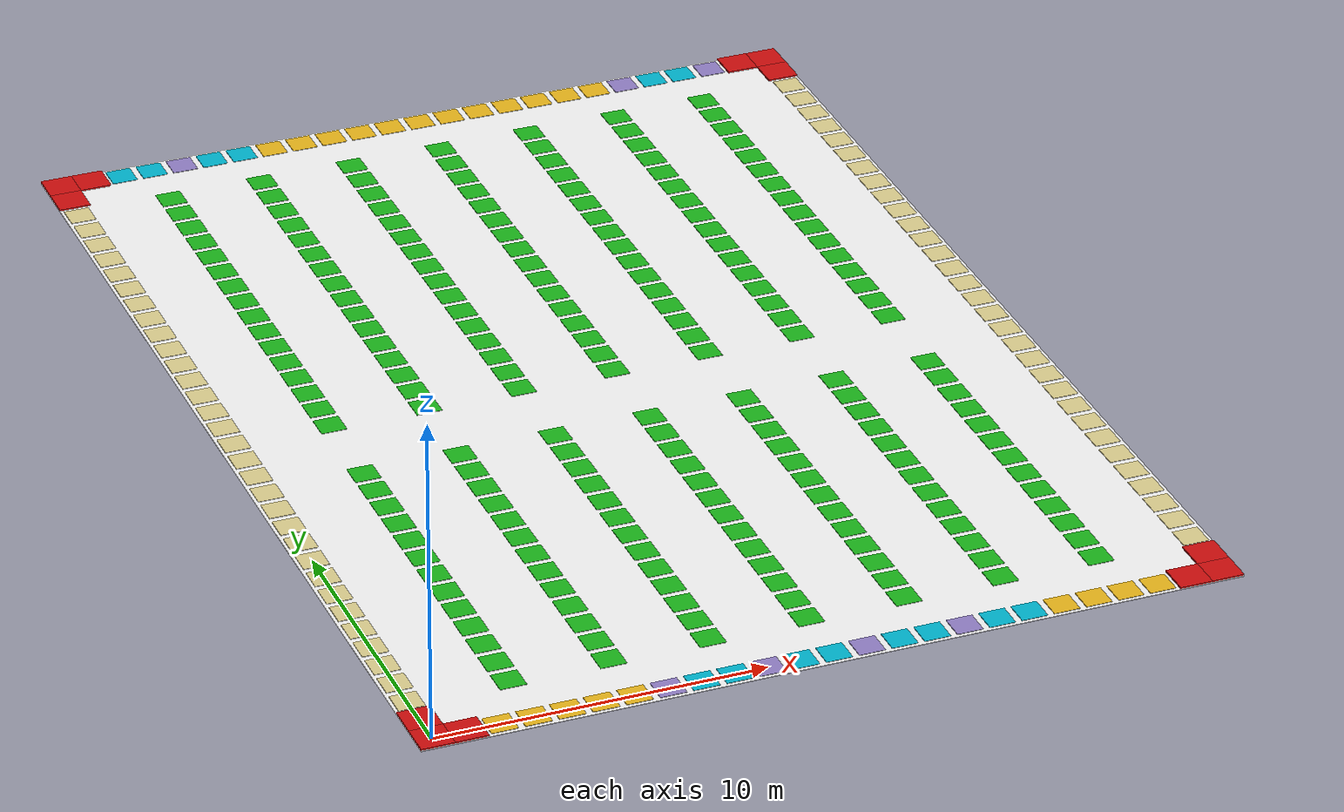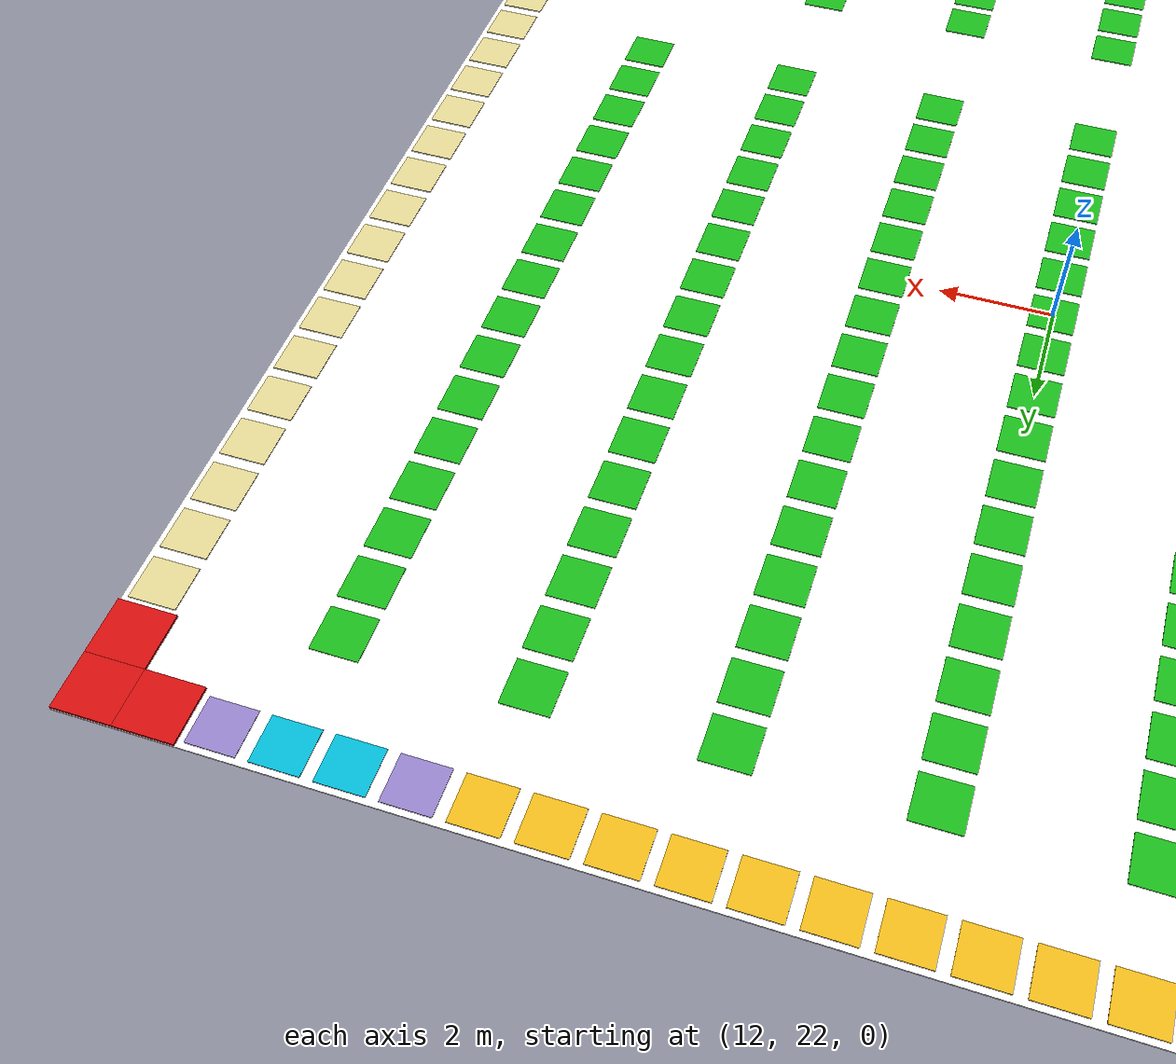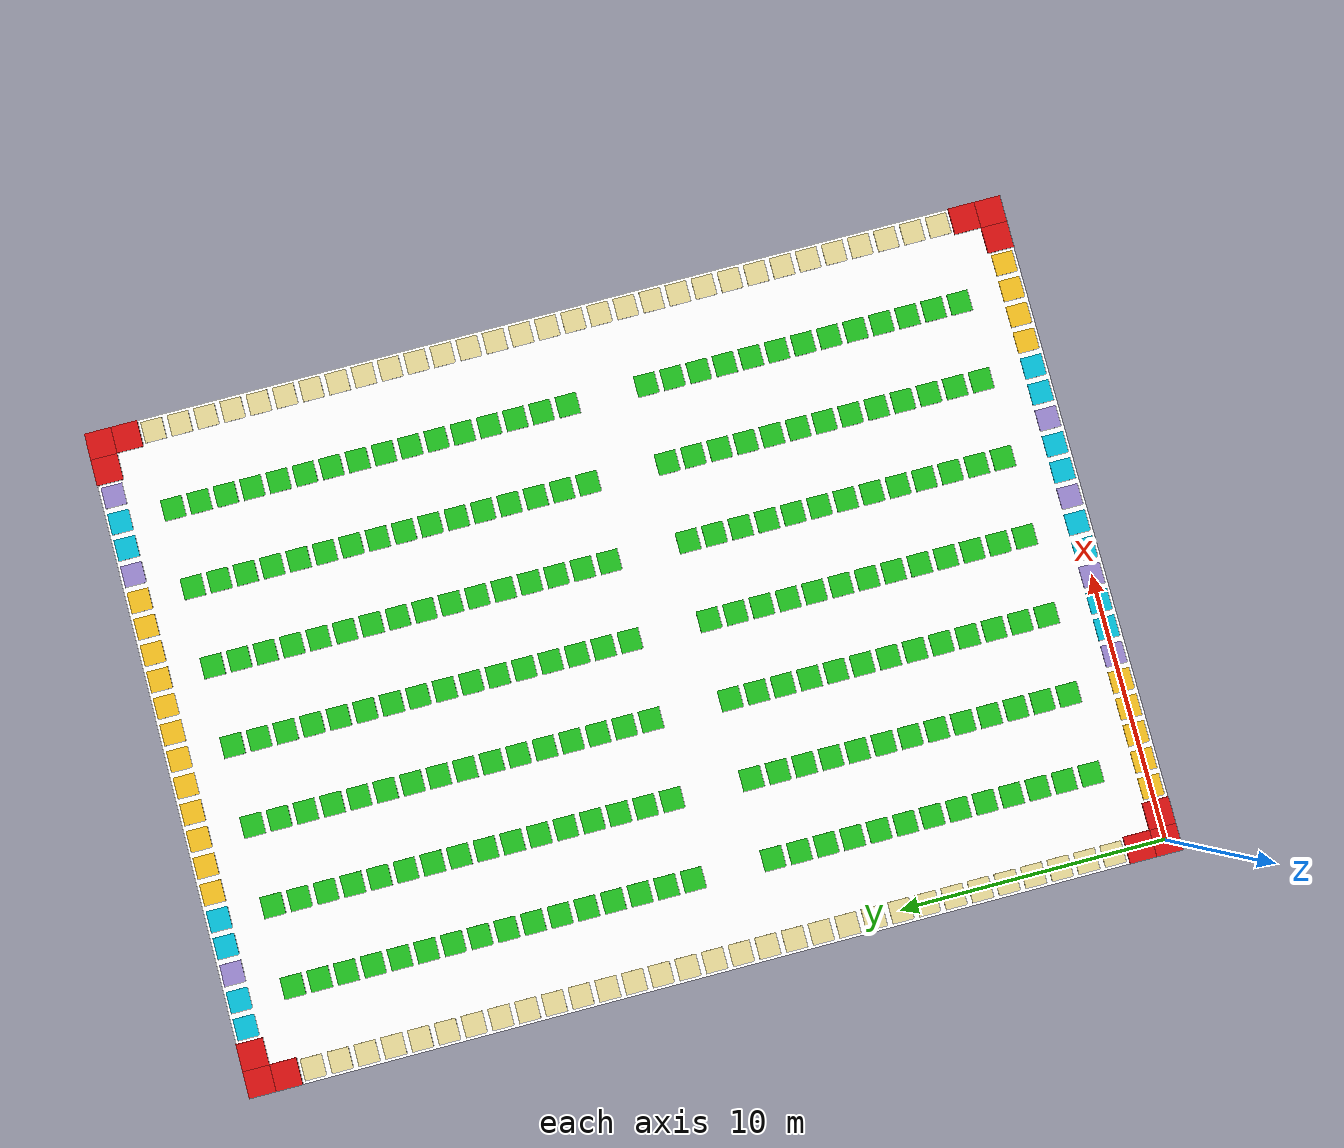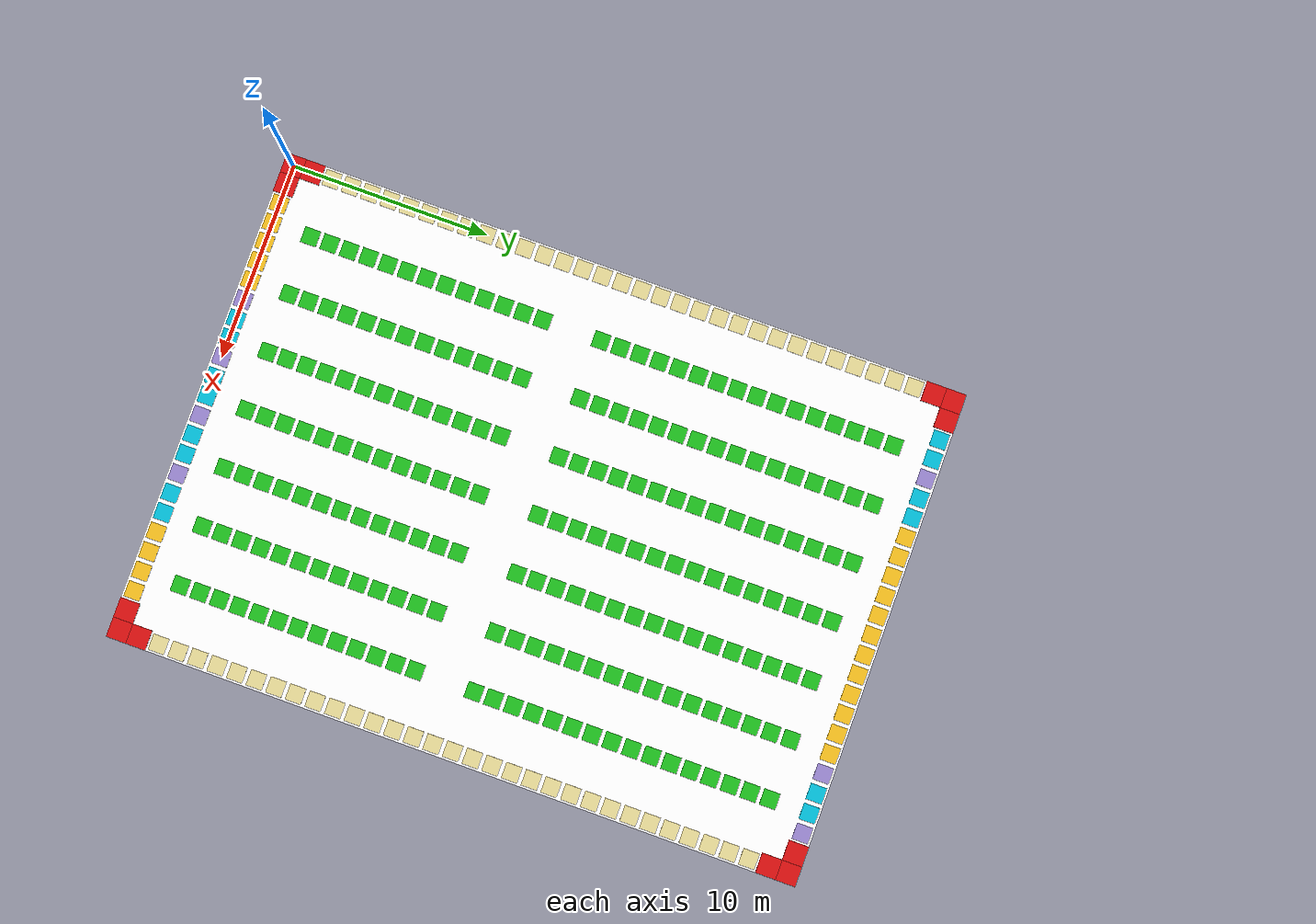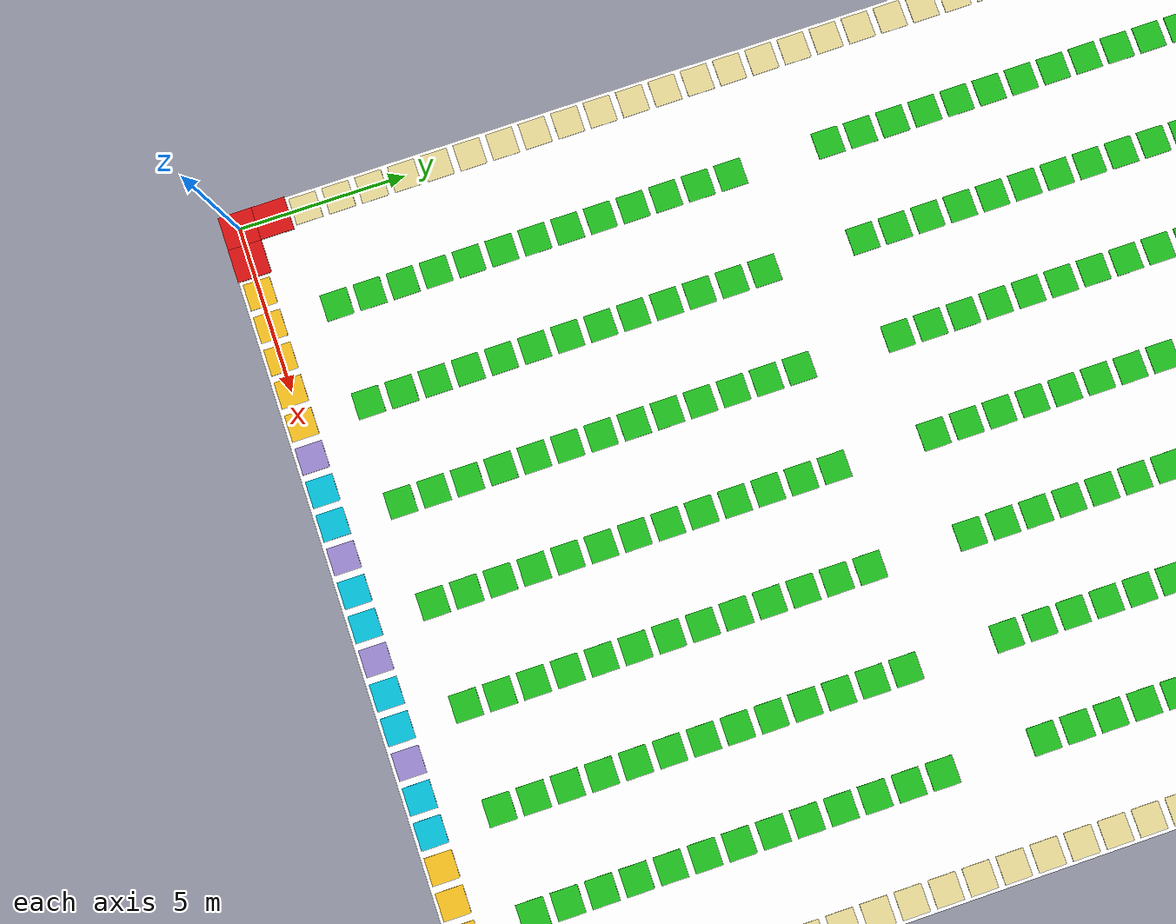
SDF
<?xml version="1.0"?>
<sdf version="1.10">
  <world name="my_map_60">

    <plugin
      filename="gz-sim-physics-system"
      name="gz::sim::systems::Physics">
    </plugin>

    <plugin
      filename="gz-sim-user-commands-system"
      name="gz::sim::systems::UserCommands">
    </plugin>

    <plugin
      filename="gz-sim-scene-broadcaster-system"
      name="gz::sim::systems::SceneBroadcaster">
    </plugin>

    <scene>
      <ambient>0.8 0.8 0.8 1</ambient>
      <background>0.6 0.6 0.6 1</background>
      <shadows>false</shadows>
    </scene>

    <light type="directional" name="sun">
      <pose>0 0 20 0 0 0</pose>
      <direction>0 0 -1</direction>
      <diffuse>1 1 1 1</diffuse>
      <specular>0.2 0.2 0.2 1</specular>
      <cast_shadows>false</cast_shadows>
    </light>

    <model name="warehouse_floor">
      <static>true</static>

      <pose>
        12.0
        17.0
        0.0
        0 0 0
      </pose>

      <link name="floor_link">

        <visual name="floor_visual">
          <geometry>
            <box>
              <size>
                25.0
                35.0
                0.02
              </size>
            </box>
          </geometry>

          <material>
            <ambient>0.95 0.95 0.95 1</ambient>
            <diffuse>0.95 0.95 0.95 1</diffuse>
          </material>
        </visual>

      </link>
    </model>

    <model name="blocked_0000">
      <static>true</static>

      <pose>
        0.0
        0.0
        0.045
        0 0 0
      </pose>

      <link name="link">

        <visual name="visual">
          <geometry>
            <box>
              <size>
                1.0
                1.0
                0.05
              </size>
            </box>
          </geometry>

          <material>
            <ambient>0.8 0.05 0.05 1</ambient>
            <diffuse>0.8 0.05 0.05 1</diffuse>
          </material>
        </visual>

      </link>
    </model>

    <model name="blocked_0001">
      <static>true</static>

      <pose>
        0.0
        1.0
        0.045
        0 0 0
      </pose>

      <link name="link">

        <visual name="visual">
          <geometry>
            <box>
              <size>
                1.0
                1.0
                0.05
              </size>
            </box>
          </geometry>

          <material>
            <ambient>0.8 0.05 0.05 1</ambient>
            <diffuse>0.8 0.05 0.05 1</diffuse>
          </material>
        </visual>

      </link>
    </model>

    <model name="blocked_0002">
      <static>true</static>

      <pose>
        0.0
        33.0
        0.045
        0 0 0
      </pose>

      <link name="link">

        <visual name="visual">
          <geometry>
            <box>
              <size>
                1.0
                1.0
                0.05
              </size>
            </box>
          </geometry>

          <material>
            <ambient>0.8 0.05 0.05 1</ambient>
            <diffuse>0.8 0.05 0.05 1</diffuse>
          </material>
        </visual>

      </link>
    </model>

    <model name="blocked_0003">
      <static>true</static>

      <pose>
        0.0
        34.0
        0.045
        0 0 0
      </pose>

      <link name="link">

        <visual name="visual">
          <geometry>
            <box>
              <size>
                1.0
                1.0
                0.05
              </size>
            </box>
          </geometry>

          <material>
            <ambient>0.8 0.05 0.05 1</ambient>
            <diffuse>0.8 0.05 0.05 1</diffuse>
          </material>
        </visual>

      </link>
    </model>

    <model name="blocked_0004">
      <static>true</static>

      <pose>
        1.0
        0.0
        0.045
        0 0 0
      </pose>

      <link name="link">

        <visual name="visual">
          <geometry>
            <box>
              <size>
                1.0
                1.0
                0.05
              </size>
            </box>
          </geometry>

          <material>
            <ambient>0.8 0.05 0.05 1</ambient>
            <diffuse>0.8 0.05 0.05 1</diffuse>
          </material>
        </visual>

      </link>
    </model>

    <model name="blocked_0005">
      <static>true</static>

      <pose>
        1.0
        34.0
        0.045
        0 0 0
      </pose>

      <link name="link">

        <visual name="visual">
          <geometry>
            <box>
              <size>
                1.0
                1.0
                0.05
              </size>
            </box>
          </geometry>

          <material>
            <ambient>0.8 0.05 0.05 1</ambient>
            <diffuse>0.8 0.05 0.05 1</diffuse>
          </material>
        </visual>

      </link>
    </model>

    <model name="blocked_0006">
      <static>true</static>

      <pose>
        23.0
        0.0
        0.045
        0 0 0
      </pose>

      <link name="link">

        <visual name="visual">
          <geometry>
            <box>
              <size>
                1.0
                1.0
                0.05
              </size>
            </box>
          </geometry>

          <material>
            <ambient>0.8 0.05 0.05 1</ambient>
            <diffuse>0.8 0.05 0.05 1</diffuse>
          </material>
        </visual>

      </link>
    </model>

    <model name="blocked_0007">
      <static>true</static>

      <pose>
        23.0
        34.0
        0.045
        0 0 0
      </pose>

      <link name="link">

        <visual name="visual">
          <geometry>
            <box>
              <size>
                1.0
                1.0
                0.05
              </size>
            </box>
          </geometry>

          <material>
            <ambient>0.8 0.05 0.05 1</ambient>
            <diffuse>0.8 0.05 0.05 1</diffuse>
          </material>
        </visual>

      </link>
    </model>

    <model name="blocked_0008">
      <static>true</static>

      <pose>
        24.0
        0.0
        0.045
        0 0 0
      </pose>

      <link name="link">

        <visual name="visual">
          <geometry>
            <box>
              <size>
                1.0
                1.0
                0.05
              </size>
            </box>
          </geometry>

          <material>
            <ambient>0.8 0.05 0.05 1</ambient>
            <diffuse>0.8 0.05 0.05 1</diffuse>
          </material>
        </visual>

      </link>
    </model>

    <model name="blocked_0009">
      <static>true</static>

      <pose>
        24.0
        1.0
        0.045
        0 0 0
      </pose>

      <link name="link">

        <visual name="visual">
          <geometry>
            <box>
              <size>
                1.0
                1.0
                0.05
              </size>
            </box>
          </geometry>

          <material>
            <ambient>0.8 0.05 0.05 1</ambient>
            <diffuse>0.8 0.05 0.05 1</diffuse>
          </material>
        </visual>

      </link>
    </model>

    <model name="blocked_0010">
      <static>true</static>

      <pose>
        24.0
        33.0
        0.045
        0 0 0
      </pose>

      <link name="link">

        <visual name="visual">
          <geometry>
            <box>
              <size>
                1.0
                1.0
                0.05
              </size>
            </box>
          </geometry>

          <material>
            <ambient>0.8 0.05 0.05 1</ambient>
            <diffuse>0.8 0.05 0.05 1</diffuse>
          </material>
        </visual>

      </link>
    </model>

    <model name="blocked_0011">
      <static>true</static>

      <pose>
        24.0
        34.0
        0.045
        0 0 0
      </pose>

      <link name="link">

        <visual name="visual">
          <geometry>
            <box>
              <size>
                1.0
                1.0
                0.05
              </size>
            </box>
          </geometry>

          <material>
            <ambient>0.8 0.05 0.05 1</ambient>
            <diffuse>0.8 0.05 0.05 1</diffuse>
          </material>
        </visual>

      </link>
    </model>

    <model name="charging_001">
      <static>true</static>

      <pose>
        2.0
        34.0
        0.02
        0 0 0
      </pose>

      <link name="link">

        <visual name="visual">
          <geometry>
            <box>
              <size>
                0.8
                0.8
                0.02
              </size>
            </box>
          </geometry>

          <material>
            <ambient>0.00 0.70 0.80 1</ambient>
            <diffuse>0.00 0.70 0.80 1</diffuse>
          </material>
        </visual>

      </link>
    </model>

    <model name="charging_002">
      <static>true</static>

      <pose>
        3.0
        34.0
        0.02
        0 0 0
      </pose>

      <link name="link">

        <visual name="visual">
          <geometry>
            <box>
              <size>
                0.8
                0.8
                0.02
              </size>
            </box>
          </geometry>

          <material>
            <ambient>0.00 0.70 0.80 1</ambient>
            <diffuse>0.00 0.70 0.80 1</diffuse>
          </material>
        </visual>

      </link>
    </model>

    <model name="charge_queue_001">
      <static>true</static>

      <pose>
        4.0
        34.0
        0.02
        0 0 0
      </pose>

      <link name="link">

        <visual name="visual">
          <geometry>
            <box>
              <size>
                0.8
                0.8
                0.02
              </size>
            </box>
          </geometry>

          <material>
            <ambient>0.56 0.49 0.76 1</ambient>
            <diffuse>0.56 0.49 0.76 1</diffuse>
          </material>
        </visual>

      </link>
    </model>

    <model name="charging_003">
      <static>true</static>

      <pose>
        5.0
        34.0
        0.02
        0 0 0
      </pose>

      <link name="link">

        <visual name="visual">
          <geometry>
            <box>
              <size>
                0.8
                0.8
                0.02
              </size>
            </box>
          </geometry>

          <material>
            <ambient>0.00 0.70 0.80 1</ambient>
            <diffuse>0.00 0.70 0.80 1</diffuse>
          </material>
        </visual>

      </link>
    </model>

    <model name="charging_004">
      <static>true</static>

      <pose>
        6.0
        34.0
        0.02
        0 0 0
      </pose>

      <link name="link">

        <visual name="visual">
          <geometry>
            <box>
              <size>
                0.8
                0.8
                0.02
              </size>
            </box>
          </geometry>

          <material>
            <ambient>0.00 0.70 0.80 1</ambient>
            <diffuse>0.00 0.70 0.80 1</diffuse>
          </material>
        </visual>

      </link>
    </model>

    <model name="dropoff_001">
      <static>true</static>

      <pose>
        7.0
        34.0
        0.02
        0 0 0
      </pose>

      <link name="link">

        <visual name="visual">
          <geometry>
            <box>
              <size>
                0.8
                0.8
                0.02
              </size>
            </box>
          </geometry>

          <material>
            <ambient>0.90 0.70 0.10 1</ambient>
            <diffuse>0.90 0.70 0.10 1</diffuse>
          </material>
        </visual>

      </link>
    </model>

    <model name="dropoff_002">
      <static>true</static>

      <pose>
        8.0
        34.0
        0.02
        0 0 0
      </pose>

      <link name="link">

        <visual name="visual">
          <geometry>
            <box>
              <size>
                0.8
                0.8
                0.02
              </size>
            </box>
          </geometry>

          <material>
            <ambient>0.90 0.70 0.10 1</ambient>
            <diffuse>0.90 0.70 0.10 1</diffuse>
          </material>
        </visual>

      </link>
    </model>

    <model name="dropoff_003">
      <static>true</static>

      <pose>
        9.0
        34.0
        0.02
        0 0 0
      </pose>

      <link name="link">

        <visual name="visual">
          <geometry>
            <box>
              <size>
                0.8
                0.8
                0.02
              </size>
            </box>
          </geometry>

          <material>
            <ambient>0.90 0.70 0.10 1</ambient>
            <diffuse>0.90 0.70 0.10 1</diffuse>
          </material>
        </visual>

      </link>
    </model>

    <model name="dropoff_004">
      <static>true</static>

      <pose>
        10.0
        34.0
        0.02
        0 0 0
      </pose>

      <link name="link">

        <visual name="visual">
          <geometry>
            <box>
              <size>
                0.8
                0.8
                0.02
              </size>
            </box>
          </geometry>

          <material>
            <ambient>0.90 0.70 0.10 1</ambient>
            <diffuse>0.90 0.70 0.10 1</diffuse>
          </material>
        </visual>

      </link>
    </model>

    <model name="dropoff_005">
      <static>true</static>

      <pose>
        11.0
        34.0
        0.02
        0 0 0
      </pose>

      <link name="link">

        <visual name="visual">
          <geometry>
            <box>
              <size>
                0.8
                0.8
                0.02
              </size>
            </box>
          </geometry>

          <material>
            <ambient>0.90 0.70 0.10 1</ambient>
            <diffuse>0.90 0.70 0.10 1</diffuse>
          </material>
        </visual>

      </link>
    </model>

    <model name="dropoff_006">
      <static>true</static>

      <pose>
        12.0
        34.0
        0.02
        0 0 0
      </pose>

      <link name="link">

        <visual name="visual">
          <geometry>
            <box>
              <size>
                0.8
                0.8
                0.02
              </size>
            </box>
          </geometry>

          <material>
            <ambient>0.90 0.70 0.10 1</ambient>
            <diffuse>0.90 0.70 0.10 1</diffuse>
          </material>
        </visual>

      </link>
    </model>

    <model name="dropoff_007">
      <static>true</static>

      <pose>
        13.0
        34.0
        0.02
        0 0 0
      </pose>

      <link name="link">

        <visual name="visual">
          <geometry>
            <box>
              <size>
                0.8
                0.8
                0.02
              </size>
            </box>
          </geometry>

          <material>
            <ambient>0.90 0.70 0.10 1</ambient>
            <diffuse>0.90 0.70 0.10 1</diffuse>
          </material>
        </visual>

      </link>
    </model>

    <model name="dropoff_008">
      <static>true</static>

      <pose>
        14.0
        34.0
        0.02
        0 0 0
      </pose>

      <link name="link">

        <visual name="visual">
          <geometry>
            <box>
              <size>
                0.8
                0.8
                0.02
              </size>
            </box>
          </geometry>

          <material>
            <ambient>0.90 0.70 0.10 1</ambient>
            <diffuse>0.90 0.70 0.10 1</diffuse>
          </material>
        </visual>

      </link>
    </model>

    <model name="dropoff_009">
      <static>true</static>

      <pose>
        15.0
        34.0
        0.02
        0 0 0
      </pose>

      <link name="link">

        <visual name="visual">
          <geometry>
            <box>
              <size>
                0.8
                0.8
                0.02
              </size>
            </box>
          </geometry>

          <material>
            <ambient>0.90 0.70 0.10 1</ambient>
            <diffuse>0.90 0.70 0.10 1</diffuse>
          </material>
        </visual>

      </link>
    </model>

    <model name="dropoff_010">
      <static>true</static>

      <pose>
        16.0
        34.0
        0.02
        0 0 0
      </pose>

      <link name="link">

        <visual name="visual">
          <geometry>
            <box>
              <size>
                0.8
                0.8
                0.02
              </size>
            </box>
          </geometry>

          <material>
            <ambient>0.90 0.70 0.10 1</ambient>
            <diffuse>0.90 0.70 0.10 1</diffuse>
          </material>
        </visual>

      </link>
    </model>

    <model name="dropoff_011">
      <static>true</static>

      <pose>
        17.0
        34.0
        0.02
        0 0 0
      </pose>

      <link name="link">

        <visual name="visual">
          <geometry>
            <box>
              <size>
                0.8
                0.8
                0.02
              </size>
            </box>
          </geometry>

          <material>
            <ambient>0.90 0.70 0.10 1</ambient>
            <diffuse>0.90 0.70 0.10 1</diffuse>
          </material>
        </visual>

      </link>
    </model>

    <model name="dropoff_012">
      <static>true</static>

      <pose>
        18.0
        34.0
        0.02
        0 0 0
      </pose>

      <link name="link">

        <visual name="visual">
          <geometry>
            <box>
              <size>
                0.8
                0.8
                0.02
              </size>
            </box>
          </geometry>

          <material>
            <ambient>0.90 0.70 0.10 1</ambient>
            <diffuse>0.90 0.70 0.10 1</diffuse>
          </material>
        </visual>

      </link>
    </model>

    <model name="charge_queue_002">
      <static>true</static>

      <pose>
        19.0
        34.0
        0.02
        0 0 0
      </pose>

      <link name="link">

        <visual name="visual">
          <geometry>
            <box>
              <size>
                0.8
                0.8
                0.02
              </size>
            </box>
          </geometry>

          <material>
            <ambient>0.56 0.49 0.76 1</ambient>
            <diffuse>0.56 0.49 0.76 1</diffuse>
          </material>
        </visual>

      </link>
    </model>

    <model name="charging_005">
      <static>true</static>

      <pose>
        20.0
        34.0
        0.02
        0 0 0
      </pose>

      <link name="link">

        <visual name="visual">
          <geometry>
            <box>
              <size>
                0.8
                0.8
                0.02
              </size>
            </box>
          </geometry>

          <material>
            <ambient>0.00 0.70 0.80 1</ambient>
            <diffuse>0.00 0.70 0.80 1</diffuse>
          </material>
        </visual>

      </link>
    </model>

    <model name="charging_006">
      <static>true</static>

      <pose>
        21.0
        34.0
        0.02
        0 0 0
      </pose>

      <link name="link">

        <visual name="visual">
          <geometry>
            <box>
              <size>
                0.8
                0.8
                0.02
              </size>
            </box>
          </geometry>

          <material>
            <ambient>0.00 0.70 0.80 1</ambient>
            <diffuse>0.00 0.70 0.80 1</diffuse>
          </material>
        </visual>

      </link>
    </model>

    <model name="charge_queue_003">
      <static>true</static>

      <pose>
        22.0
        34.0
        0.02
        0 0 0
      </pose>

      <link name="link">

        <visual name="visual">
          <geometry>
            <box>
              <size>
                0.8
                0.8
                0.02
              </size>
            </box>
          </geometry>

          <material>
            <ambient>0.56 0.49 0.76 1</ambient>
            <diffuse>0.56 0.49 0.76 1</diffuse>
          </material>
        </visual>

      </link>
    </model>

    <model name="staging_001">
      <static>true</static>

      <pose>
        0.0
        32.0
        0.02
        0 0 0
      </pose>

      <link name="link">

        <visual name="visual">
          <geometry>
            <box>
              <size>
                0.8
                0.8
                0.02
              </size>
            </box>
          </geometry>

          <material>
            <ambient>0.85 0.80 0.55 1</ambient>
            <diffuse>0.85 0.80 0.55 1</diffuse>
          </material>
        </visual>

      </link>
    </model>

    <model name="shelf_001">
      <static>true</static>

      <pose>
        3.0
        32.0
        0.02
        0 0 0
      </pose>

      <link name="link">

        <visual name="visual">
          <geometry>
            <box>
              <size>
                0.8
                0.8
                0.02
              </size>
            </box>
          </geometry>

          <material>
            <ambient>0.10 0.70 0.10 1</ambient>
            <diffuse>0.10 0.70 0.10 1</diffuse>
          </material>
        </visual>

      </link>
    </model>

    <model name="shelf_002">
      <static>true</static>

      <pose>
        6.0
        32.0
        0.02
        0 0 0
      </pose>

      <link name="link">

        <visual name="visual">
          <geometry>
            <box>
              <size>
                0.8
                0.8
                0.02
              </size>
            </box>
          </geometry>

          <material>
            <ambient>0.10 0.70 0.10 1</ambient>
            <diffuse>0.10 0.70 0.10 1</diffuse>
          </material>
        </visual>

      </link>
    </model>

    <model name="shelf_003">
      <static>true</static>

      <pose>
        9.0
        32.0
        0.02
        0 0 0
      </pose>

      <link name="link">

        <visual name="visual">
          <geometry>
            <box>
              <size>
                0.8
                0.8
                0.02
              </size>
            </box>
          </geometry>

          <material>
            <ambient>0.10 0.70 0.10 1</ambient>
            <diffuse>0.10 0.70 0.10 1</diffuse>
          </material>
        </visual>

      </link>
    </model>

    <model name="shelf_004">
      <static>true</static>

      <pose>
        12.0
        32.0
        0.02
        0 0 0
      </pose>

      <link name="link">

        <visual name="visual">
          <geometry>
            <box>
              <size>
                0.8
                0.8
                0.02
              </size>
            </box>
          </geometry>

          <material>
            <ambient>0.10 0.70 0.10 1</ambient>
            <diffuse>0.10 0.70 0.10 1</diffuse>
          </material>
        </visual>

      </link>
    </model>

    <model name="shelf_005">
      <static>true</static>

      <pose>
        15.0
        32.0
        0.02
        0 0 0
      </pose>

      <link name="link">

        <visual name="visual">
          <geometry>
            <box>
              <size>
                0.8
                0.8
                0.02
              </size>
            </box>
          </geometry>

          <material>
            <ambient>0.10 0.70 0.10 1</ambient>
            <diffuse>0.10 0.70 0.10 1</diffuse>
          </material>
        </visual>

      </link>
    </model>

    <model name="shelf_006">
      <static>true</static>

      <pose>
        18.0
        32.0
        0.02
        0 0 0
      </pose>

      <link name="link">

        <visual name="visual">
          <geometry>
            <box>
              <size>
                0.8
                0.8
                0.02
              </size>
            </box>
          </geometry>

          <material>
            <ambient>0.10 0.70 0.10 1</ambient>
            <diffuse>0.10 0.70 0.10 1</diffuse>
          </material>
        </visual>

      </link>
    </model>

    <model name="shelf_007">
      <static>true</static>

      <pose>
        21.0
        32.0
        0.02
        0 0 0
      </pose>

      <link name="link">

        <visual name="visual">
          <geometry>
            <box>
              <size>
                0.8
                0.8
                0.02
              </size>
            </box>
          </geometry>

          <material>
            <ambient>0.10 0.70 0.10 1</ambient>
            <diffuse>0.10 0.70 0.10 1</diffuse>
          </material>
        </visual>

      </link>
    </model>

    <model name="staging_002">
      <static>true</static>

      <pose>
        24.0
        32.0
        0.02
        0 0 0
      </pose>

      <link name="link">

        <visual name="visual">
          <geometry>
            <box>
              <size>
                0.8
                0.8
                0.02
              </size>
            </box>
          </geometry>

          <material>
            <ambient>0.85 0.80 0.55 1</ambient>
            <diffuse>0.85 0.80 0.55 1</diffuse>
          </material>
        </visual>

      </link>
    </model>

    <model name="staging_003">
      <static>true</static>

      <pose>
        0.0
        31.0
        0.02
        0 0 0
      </pose>

      <link name="link">

        <visual name="visual">
          <geometry>
            <box>
              <size>
                0.8
                0.8
                0.02
              </size>
            </box>
          </geometry>

          <material>
            <ambient>0.85 0.80 0.55 1</ambient>
            <diffuse>0.85 0.80 0.55 1</diffuse>
          </material>
        </visual>

      </link>
    </model>

    <model name="shelf_008">
      <static>true</static>

      <pose>
        3.0
        31.0
        0.02
        0 0 0
      </pose>

      <link name="link">

        <visual name="visual">
          <geometry>
            <box>
              <size>
                0.8
                0.8
                0.02
              </size>
            </box>
          </geometry>

          <material>
            <ambient>0.10 0.70 0.10 1</ambient>
            <diffuse>0.10 0.70 0.10 1</diffuse>
          </material>
        </visual>

      </link>
    </model>

    <model name="shelf_009">
      <static>true</static>

      <pose>
        6.0
        31.0
        0.02
        0 0 0
      </pose>

      <link name="link">

        <visual name="visual">
          <geometry>
            <box>
              <size>
                0.8
                0.8
                0.02
              </size>
            </box>
          </geometry>

          <material>
            <ambient>0.10 0.70 0.10 1</ambient>
            <diffuse>0.10 0.70 0.10 1</diffuse>
          </material>
        </visual>

      </link>
    </model>

    <model name="shelf_010">
      <static>true</static>

      <pose>
        9.0
        31.0
        0.02
        0 0 0
      </pose>

      <link name="link">

        <visual name="visual">
          <geometry>
            <box>
              <size>
                0.8
                0.8
                0.02
              </size>
            </box>
          </geometry>

          <material>
            <ambient>0.10 0.70 0.10 1</ambient>
            <diffuse>0.10 0.70 0.10 1</diffuse>
          </material>
        </visual>

      </link>
    </model>

    <model name="shelf_011">
      <static>true</static>

      <pose>
        12.0
        31.0
        0.02
        0 0 0
      </pose>

      <link name="link">

        <visual name="visual">
          <geometry>
            <box>
              <size>
                0.8
                0.8
                0.02
              </size>
            </box>
          </geometry>

          <material>
            <ambient>0.10 0.70 0.10 1</ambient>
            <diffuse>0.10 0.70 0.10 1</diffuse>
          </material>
        </visual>

      </link>
    </model>

    <model name="shelf_012">
      <static>true</static>

      <pose>
        15.0
        31.0
        0.02
        0 0 0
      </pose>

      <link name="link">

        <visual name="visual">
          <geometry>
            <box>
              <size>
                0.8
                0.8
                0.02
              </size>
            </box>
          </geometry>

          <material>
            <ambient>0.10 0.70 0.10 1</ambient>
            <diffuse>0.10 0.70 0.10 1</diffuse>
          </material>
        </visual>

      </link>
    </model>

    <model name="shelf_013">
      <static>true</static>

      <pose>
        18.0
        31.0
        0.02
        0 0 0
      </pose>

      <link name="link">

        <visual name="visual">
          <geometry>
            <box>
              <size>
                0.8
                0.8
                0.02
              </size>
            </box>
          </geometry>

          <material>
            <ambient>0.10 0.70 0.10 1</ambient>
            <diffuse>0.10 0.70 0.10 1</diffuse>
          </material>
        </visual>

      </link>
    </model>

    <model name="shelf_014">
      <static>true</static>

      <pose>
        21.0
        31.0
        0.02
        0 0 0
      </pose>

      <link name="link">

        <visual name="visual">
          <geometry>
            <box>
              <size>
                0.8
                0.8
                0.02
              </size>
            </box>
          </geometry>

          <material>
            <ambient>0.10 0.70 0.10 1</ambient>
            <diffuse>0.10 0.70 0.10 1</diffuse>
          </material>
        </visual>

      </link>
    </model>

    <model name="staging_004">
      <static>true</static>

      <pose>
        24.0
        31.0
        0.02
        0 0 0
      </pose>

      <link name="link">

        <visual name="visual">
          <geometry>
            <box>
              <size>
                0.8
                0.8
                0.02
              </size>
            </box>
          </geometry>

          <material>
            <ambient>0.85 0.80 0.55 1</ambient>
            <diffuse>0.85 0.80 0.55 1</diffuse>
          </material>
        </visual>

      </link>
    </model>

    <model name="staging_005">
      <static>true</static>

      <pose>
        0.0
        30.0
        0.02
        0 0 0
      </pose>

      <link name="link">

        <visual name="visual">
          <geometry>
            <box>
              <size>
                0.8
                0.8
                0.02
              </size>
            </box>
          </geometry>

          <material>
            <ambient>0.85 0.80 0.55 1</ambient>
            <diffuse>0.85 0.80 0.55 1</diffuse>
          </material>
        </visual>

      </link>
    </model>

    <model name="shelf_015">
      <static>true</static>

      <pose>
        3.0
        30.0
        0.02
        0 0 0
      </pose>

      <link name="link">

        <visual name="visual">
          <geometry>
            <box>
              <size>
                0.8
                0.8
                0.02
              </size>
            </box>
          </geometry>

          <material>
            <ambient>0.10 0.70 0.10 1</ambient>
            <diffuse>0.10 0.70 0.10 1</diffuse>
          </material>
        </visual>

      </link>
    </model>

    <model name="shelf_016">
      <static>true</static>

      <pose>
        6.0
        30.0
        0.02
        0 0 0
      </pose>

      <link name="link">

        <visual name="visual">
          <geometry>
            <box>
              <size>
                0.8
                0.8
                0.02
              </size>
            </box>
          </geometry>

          <material>
            <ambient>0.10 0.70 0.10 1</ambient>
            <diffuse>0.10 0.70 0.10 1</diffuse>
          </material>
        </visual>

      </link>
    </model>

    <model name="shelf_017">
      <static>true</static>

      <pose>
        9.0
        30.0
        0.02
        0 0 0
      </pose>

      <link name="link">

        <visual name="visual">
          <geometry>
            <box>
              <size>
                0.8
                0.8
                0.02
              </size>
            </box>
          </geometry>

          <material>
            <ambient>0.10 0.70 0.10 1</ambient>
            <diffuse>0.10 0.70 0.10 1</diffuse>
          </material>
        </visual>

      </link>
    </model>

    <model name="shelf_018">
      <static>true</static>

      <pose>
        12.0
        30.0
        0.02
        0 0 0
      </pose>

      <link name="link">

        <visual name="visual">
          <geometry>
            <box>
              <size>
                0.8
                0.8
                0.02
              </size>
            </box>
          </geometry>

          <material>
            <ambient>0.10 0.70 0.10 1</ambient>
            <diffuse>0.10 0.70 0.10 1</diffuse>
          </material>
        </visual>

      </link>
    </model>

    <model name="shelf_019">
      <static>true</static>

      <pose>
        15.0
        30.0
        0.02
        0 0 0
      </pose>

      <link name="link">

        <visual name="visual">
          <geometry>
            <box>
              <size>
                0.8
                0.8
                0.02
              </size>
            </box>
          </geometry>

          <material>
            <ambient>0.10 0.70 0.10 1</ambient>
            <diffuse>0.10 0.70 0.10 1</diffuse>
          </material>
        </visual>

      </link>
    </model>

    <model name="shelf_020">
      <static>true</static>

      <pose>
        18.0
        30.0
        0.02
        0 0 0
      </pose>

      <link name="link">

        <visual name="visual">
          <geometry>
            <box>
              <size>
                0.8
                0.8
                0.02
              </size>
            </box>
          </geometry>

          <material>
            <ambient>0.10 0.70 0.10 1</ambient>
            <diffuse>0.10 0.70 0.10 1</diffuse>
          </material>
        </visual>

      </link>
    </model>

    <model name="shelf_021">
      <static>true</static>

      <pose>
        21.0
        30.0
        0.02
        0 0 0
      </pose>

      <link name="link">

        <visual name="visual">
          <geometry>
            <box>
              <size>
                0.8
                0.8
                0.02
              </size>
            </box>
          </geometry>

          <material>
            <ambient>0.10 0.70 0.10 1</ambient>
            <diffuse>0.10 0.70 0.10 1</diffuse>
          </material>
        </visual>

      </link>
    </model>

    <model name="staging_006">
      <static>true</static>

      <pose>
        24.0
        30.0
        0.02
        0 0 0
      </pose>

      <link name="link">

        <visual name="visual">
          <geometry>
            <box>
              <size>
                0.8
                0.8
                0.02
              </size>
            </box>
          </geometry>

          <material>
            <ambient>0.85 0.80 0.55 1</ambient>
            <diffuse>0.85 0.80 0.55 1</diffuse>
          </material>
        </visual>

      </link>
    </model>

    <model name="staging_007">
      <static>true</static>

      <pose>
        0.0
        29.0
        0.02
        0 0 0
      </pose>

      <link name="link">

        <visual name="visual">
          <geometry>
            <box>
              <size>
                0.8
                0.8
                0.02
              </size>
            </box>
          </geometry>

          <material>
            <ambient>0.85 0.80 0.55 1</ambient>
            <diffuse>0.85 0.80 0.55 1</diffuse>
          </material>
        </visual>

      </link>
    </model>

    <model name="shelf_022">
      <static>true</static>

      <pose>
        3.0
        29.0
        0.02
        0 0 0
      </pose>

      <link name="link">

        <visual name="visual">
          <geometry>
            <box>
              <size>
                0.8
                0.8
                0.02
              </size>
            </box>
          </geometry>

          <material>
            <ambient>0.10 0.70 0.10 1</ambient>
            <diffuse>0.10 0.70 0.10 1</diffuse>
          </material>
        </visual>

      </link>
    </model>

    <model name="shelf_023">
      <static>true</static>

      <pose>
        6.0
        29.0
        0.02
        0 0 0
      </pose>

      <link name="link">

        <visual name="visual">
          <geometry>
            <box>
              <size>
                0.8
                0.8
                0.02
              </size>
            </box>
          </geometry>

          <material>
            <ambient>0.10 0.70 0.10 1</ambient>
            <diffuse>0.10 0.70 0.10 1</diffuse>
          </material>
        </visual>

      </link>
    </model>

    <model name="shelf_024">
      <static>true</static>

      <pose>
        9.0
        29.0
        0.02
        0 0 0
      </pose>

      <link name="link">

        <visual name="visual">
          <geometry>
            <box>
              <size>
                0.8
                0.8
                0.02
              </size>
            </box>
          </geometry>

          <material>
            <ambient>0.10 0.70 0.10 1</ambient>
            <diffuse>0.10 0.70 0.10 1</diffuse>
          </material>
        </visual>

      </link>
    </model>

    <model name="shelf_025">
      <static>true</static>

      <pose>
        12.0
        29.0
        0.02
        0 0 0
      </pose>

      <link name="link">

        <visual name="visual">
          <geometry>
            <box>
              <size>
                0.8
                0.8
                0.02
              </size>
            </box>
          </geometry>

          <material>
            <ambient>0.10 0.70 0.10 1</ambient>
            <diffuse>0.10 0.70 0.10 1</diffuse>
          </material>
        </visual>

      </link>
    </model>

    <model name="shelf_026">
      <static>true</static>

      <pose>
        15.0
        29.0
        0.02
        0 0 0
      </pose>

      <link name="link">

        <visual name="visual">
          <geometry>
            <box>
              <size>
                0.8
                0.8
                0.02
              </size>
            </box>
          </geometry>

          <material>
            <ambient>0.10 0.70 0.10 1</ambient>
            <diffuse>0.10 0.70 0.10 1</diffuse>
          </material>
        </visual>

      </link>
    </model>

    <model name="shelf_027">
      <static>true</static>

      <pose>
        18.0
        29.0
        0.02
        0 0 0
      </pose>

      <link name="link">

        <visual name="visual">
          <geometry>
            <box>
              <size>
                0.8
                0.8
                0.02
              </size>
            </box>
          </geometry>

          <material>
            <ambient>0.10 0.70 0.10 1</ambient>
            <diffuse>0.10 0.70 0.10 1</diffuse>
          </material>
        </visual>

      </link>
    </model>

    <model name="shelf_028">
      <static>true</static>

      <pose>
        21.0
        29.0
        0.02
        0 0 0
      </pose>

      <link name="link">

        <visual name="visual">
          <geometry>
            <box>
              <size>
                0.8
                0.8
                0.02
              </size>
            </box>
          </geometry>

          <material>
            <ambient>0.10 0.70 0.10 1</ambient>
            <diffuse>0.10 0.70 0.10 1</diffuse>
          </material>
        </visual>

      </link>
    </model>

    <model name="staging_008">
      <static>true</static>

      <pose>
        24.0
        29.0
        0.02
        0 0 0
      </pose>

      <link name="link">

        <visual name="visual">
          <geometry>
            <box>
              <size>
                0.8
                0.8
                0.02
              </size>
            </box>
          </geometry>

          <material>
            <ambient>0.85 0.80 0.55 1</ambient>
            <diffuse>0.85 0.80 0.55 1</diffuse>
          </material>
        </visual>

      </link>
    </model>

    <model name="staging_009">
      <static>true</static>

      <pose>
        0.0
        28.0
        0.02
        0 0 0
      </pose>

      <link name="link">

        <visual name="visual">
          <geometry>
            <box>
              <size>
                0.8
                0.8
                0.02
              </size>
            </box>
          </geometry>

          <material>
            <ambient>0.85 0.80 0.55 1</ambient>
            <diffuse>0.85 0.80 0.55 1</diffuse>
          </material>
        </visual>

      </link>
    </model>

    <model name="shelf_029">
      <static>true</static>

      <pose>
        3.0
        28.0
        0.02
        0 0 0
      </pose>

      <link name="link">

        <visual name="visual">
          <geometry>
            <box>
              <size>
                0.8
                0.8
                0.02
              </size>
            </box>
          </geometry>

          <material>
            <ambient>0.10 0.70 0.10 1</ambient>
            <diffuse>0.10 0.70 0.10 1</diffuse>
          </material>
        </visual>

      </link>
    </model>

    <model name="shelf_030">
      <static>true</static>

      <pose>
        6.0
        28.0
        0.02
        0 0 0
      </pose>

      <link name="link">

        <visual name="visual">
          <geometry>
            <box>
              <size>
                0.8
                0.8
                0.02
              </size>
            </box>
          </geometry>

          <material>
            <ambient>0.10 0.70 0.10 1</ambient>
            <diffuse>0.10 0.70 0.10 1</diffuse>
          </material>
        </visual>

      </link>
    </model>

    <model name="shelf_031">
      <static>true</static>

      <pose>
        9.0
        28.0
        0.02
        0 0 0
      </pose>

      <link name="link">

        <visual name="visual">
          <geometry>
            <box>
              <size>
                0.8
                0.8
                0.02
              </size>
            </box>
          </geometry>

          <material>
            <ambient>0.10 0.70 0.10 1</ambient>
            <diffuse>0.10 0.70 0.10 1</diffuse>
          </material>
        </visual>

      </link>
    </model>

    <model name="shelf_032">
      <static>true</static>

      <pose>
        12.0
        28.0
        0.02
        0 0 0
      </pose>

      <link name="link">

        <visual name="visual">
          <geometry>
            <box>
              <size>
                0.8
                0.8
                0.02
              </size>
            </box>
          </geometry>

          <material>
            <ambient>0.10 0.70 0.10 1</ambient>
            <diffuse>0.10 0.70 0.10 1</diffuse>
          </material>
        </visual>

      </link>
    </model>

    <model name="shelf_033">
      <static>true</static>

      <pose>
        15.0
        28.0
        0.02
        0 0 0
      </pose>

      <link name="link">

        <visual name="visual">
          <geometry>
            <box>
              <size>
                0.8
                0.8
                0.02
              </size>
            </box>
          </geometry>

          <material>
            <ambient>0.10 0.70 0.10 1</ambient>
            <diffuse>0.10 0.70 0.10 1</diffuse>
          </material>
        </visual>

      </link>
    </model>

    <model name="shelf_034">
      <static>true</static>

      <pose>
        18.0
        28.0
        0.02
        0 0 0
      </pose>

      <link name="link">

        <visual name="visual">
          <geometry>
            <box>
              <size>
                0.8
                0.8
                0.02
              </size>
            </box>
          </geometry>

          <material>
            <ambient>0.10 0.70 0.10 1</ambient>
            <diffuse>0.10 0.70 0.10 1</diffuse>
          </material>
        </visual>

      </link>
    </model>

    <model name="shelf_035">
      <static>true</static>

      <pose>
        21.0
        28.0
        0.02
        0 0 0
      </pose>

      <link name="link">

        <visual name="visual">
          <geometry>
            <box>
              <size>
                0.8
                0.8
                0.02
              </size>
            </box>
          </geometry>

          <material>
            <ambient>0.10 0.70 0.10 1</ambient>
            <diffuse>0.10 0.70 0.10 1</diffuse>
          </material>
        </visual>

      </link>
    </model>

    <model name="staging_010">
      <static>true</static>

      <pose>
        24.0
        28.0
        0.02
        0 0 0
      </pose>

      <link name="link">

        <visual name="visual">
          <geometry>
            <box>
              <size>
                0.8
                0.8
                0.02
              </size>
            </box>
          </geometry>

          <material>
            <ambient>0.85 0.80 0.55 1</ambient>
            <diffuse>0.85 0.80 0.55 1</diffuse>
          </material>
        </visual>

      </link>
    </model>

    <model name="staging_011">
      <static>true</static>

      <pose>
        0.0
        27.0
        0.02
        0 0 0
      </pose>

      <link name="link">

        <visual name="visual">
          <geometry>
            <box>
              <size>
                0.8
                0.8
                0.02
              </size>
            </box>
          </geometry>

          <material>
            <ambient>0.85 0.80 0.55 1</ambient>
            <diffuse>0.85 0.80 0.55 1</diffuse>
          </material>
        </visual>

      </link>
    </model>

    <model name="shelf_036">
      <static>true</static>

      <pose>
        3.0
        27.0
        0.02
        0 0 0
      </pose>

      <link name="link">

        <visual name="visual">
          <geometry>
            <box>
              <size>
                0.8
                0.8
                0.02
              </size>
            </box>
          </geometry>

          <material>
            <ambient>0.10 0.70 0.10 1</ambient>
            <diffuse>0.10 0.70 0.10 1</diffuse>
          </material>
        </visual>

      </link>
    </model>

    <model name="shelf_037">
      <static>true</static>

      <pose>
        6.0
        27.0
        0.02
        0 0 0
      </pose>

      <link name="link">

        <visual name="visual">
          <geometry>
            <box>
              <size>
                0.8
                0.8
                0.02
              </size>
            </box>
          </geometry>

          <material>
            <ambient>0.10 0.70 0.10 1</ambient>
            <diffuse>0.10 0.70 0.10 1</diffuse>
          </material>
        </visual>

      </link>
    </model>

    <model name="shelf_038">
      <static>true</static>

      <pose>
        9.0
        27.0
        0.02
        0 0 0
      </pose>

      <link name="link">

        <visual name="visual">
          <geometry>
            <box>
              <size>
                0.8
                0.8
                0.02
              </size>
            </box>
          </geometry>

          <material>
            <ambient>0.10 0.70 0.10 1</ambient>
            <diffuse>0.10 0.70 0.10 1</diffuse>
          </material>
        </visual>

      </link>
    </model>

    <model name="shelf_039">
      <static>true</static>

      <pose>
        12.0
        27.0
        0.02
        0 0 0
      </pose>

      <link name="link">

        <visual name="visual">
          <geometry>
            <box>
              <size>
                0.8
                0.8
                0.02
              </size>
            </box>
          </geometry>

          <material>
            <ambient>0.10 0.70 0.10 1</ambient>
            <diffuse>0.10 0.70 0.10 1</diffuse>
          </material>
        </visual>

      </link>
    </model>

    <model name="shelf_040">
      <static>true</static>

      <pose>
        15.0
        27.0
        0.02
        0 0 0
      </pose>

      <link name="link">

        <visual name="visual">
          <geometry>
            <box>
              <size>
                0.8
                0.8
                0.02
              </size>
            </box>
          </geometry>

          <material>
            <ambient>0.10 0.70 0.10 1</ambient>
            <diffuse>0.10 0.70 0.10 1</diffuse>
          </material>
        </visual>

      </link>
    </model>

    <model name="shelf_041">
      <static>true</static>

      <pose>
        18.0
        27.0
        0.02
        0 0 0
      </pose>

      <link name="link">

        <visual name="visual">
          <geometry>
            <box>
              <size>
                0.8
                0.8
                0.02
              </size>
            </box>
          </geometry>

          <material>
            <ambient>0.10 0.70 0.10 1</ambient>
            <diffuse>0.10 0.70 0.10 1</diffuse>
          </material>
        </visual>

      </link>
    </model>

    <model name="shelf_042">
      <static>true</static>

      <pose>
        21.0
        27.0
        0.02
        0 0 0
      </pose>

      <link name="link">

        <visual name="visual">
          <geometry>
            <box>
              <size>
                0.8
                0.8
                0.02
              </size>
            </box>
          </geometry>

          <material>
            <ambient>0.10 0.70 0.10 1</ambient>
            <diffuse>0.10 0.70 0.10 1</diffuse>
          </material>
        </visual>

      </link>
    </model>

    <model name="staging_012">
      <static>true</static>

      <pose>
        24.0
        27.0
        0.02
        0 0 0
      </pose>

      <link name="link">

        <visual name="visual">
          <geometry>
            <box>
              <size>
                0.8
                0.8
                0.02
              </size>
            </box>
          </geometry>

          <material>
            <ambient>0.85 0.80 0.55 1</ambient>
            <diffuse>0.85 0.80 0.55 1</diffuse>
          </material>
        </visual>

      </link>
    </model>

    <model name="staging_013">
      <static>true</static>

      <pose>
        0.0
        26.0
        0.02
        0 0 0
      </pose>

      <link name="link">

        <visual name="visual">
          <geometry>
            <box>
              <size>
                0.8
                0.8
                0.02
              </size>
            </box>
          </geometry>

          <material>
            <ambient>0.85 0.80 0.55 1</ambient>
            <diffuse>0.85 0.80 0.55 1</diffuse>
          </material>
        </visual>

      </link>
    </model>

    <model name="shelf_043">
      <static>true</static>

      <pose>
        3.0
        26.0
        0.02
        0 0 0
      </pose>

      <link name="link">

        <visual name="visual">
          <geometry>
            <box>
              <size>
                0.8
                0.8
                0.02
              </size>
            </box>
          </geometry>

          <material>
            <ambient>0.10 0.70 0.10 1</ambient>
            <diffuse>0.10 0.70 0.10 1</diffuse>
          </material>
        </visual>

      </link>
    </model>

    <model name="shelf_044">
      <static>true</static>

      <pose>
        6.0
        26.0
        0.02
        0 0 0
      </pose>

      <link name="link">

        <visual name="visual">
          <geometry>
            <box>
              <size>
                0.8
                0.8
                0.02
              </size>
            </box>
          </geometry>

          <material>
            <ambient>0.10 0.70 0.10 1</ambient>
            <diffuse>0.10 0.70 0.10 1</diffuse>
          </material>
        </visual>

      </link>
    </model>

    <model name="shelf_045">
      <static>true</static>

      <pose>
        9.0
        26.0
        0.02
        0 0 0
      </pose>

      <link name="link">

        <visual name="visual">
          <geometry>
            <box>
              <size>
                0.8
                0.8
                0.02
              </size>
            </box>
          </geometry>

          <material>
            <ambient>0.10 0.70 0.10 1</ambient>
            <diffuse>0.10 0.70 0.10 1</diffuse>
          </material>
        </visual>

      </link>
    </model>

    <model name="shelf_046">
      <static>true</static>

      <pose>
        12.0
        26.0
        0.02
        0 0 0
      </pose>

      <link name="link">

        <visual name="visual">
          <geometry>
            <box>
              <size>
                0.8
                0.8
                0.02
              </size>
            </box>
          </geometry>

          <material>
            <ambient>0.10 0.70 0.10 1</ambient>
            <diffuse>0.10 0.70 0.10 1</diffuse>
          </material>
        </visual>

      </link>
    </model>

    <model name="shelf_047">
      <static>true</static>

      <pose>
        15.0
        26.0
        0.02
        0 0 0
      </pose>

      <link name="link">

        <visual name="visual">
          <geometry>
            <box>
              <size>
                0.8
                0.8
                0.02
              </size>
            </box>
          </geometry>

          <material>
            <ambient>0.10 0.70 0.10 1</ambient>
            <diffuse>0.10 0.70 0.10 1</diffuse>
          </material>
        </visual>

      </link>
    </model>

    <model name="shelf_048">
      <static>true</static>

      <pose>
        18.0
        26.0
        0.02
        0 0 0
      </pose>

      <link name="link">

        <visual name="visual">
          <geometry>
            <box>
              <size>
                0.8
                0.8
                0.02
              </size>
            </box>
          </geometry>

          <material>
            <ambient>0.10 0.70 0.10 1</ambient>
            <diffuse>0.10 0.70 0.10 1</diffuse>
          </material>
        </visual>

      </link>
    </model>

    <model name="shelf_049">
      <static>true</static>

      <pose>
        21.0
        26.0
        0.02
        0 0 0
      </pose>

      <link name="link">

        <visual name="visual">
          <geometry>
            <box>
              <size>
                0.8
                0.8
                0.02
              </size>
            </box>
          </geometry>

          <material>
            <ambient>0.10 0.70 0.10 1</ambient>
            <diffuse>0.10 0.70 0.10 1</diffuse>
          </material>
        </visual>

      </link>
    </model>

    <model name="staging_014">
      <static>true</static>

      <pose>
        24.0
        26.0
        0.02
        0 0 0
      </pose>

      <link name="link">

        <visual name="visual">
          <geometry>
            <box>
              <size>
                0.8
                0.8
                0.02
              </size>
            </box>
          </geometry>

          <material>
            <ambient>0.85 0.80 0.55 1</ambient>
            <diffuse>0.85 0.80 0.55 1</diffuse>
          </material>
        </visual>

      </link>
    </model>

    <model name="staging_015">
      <static>true</static>

      <pose>
        0.0
        25.0
        0.02
        0 0 0
      </pose>

      <link name="link">

        <visual name="visual">
          <geometry>
            <box>
              <size>
                0.8
                0.8
                0.02
              </size>
            </box>
          </geometry>

          <material>
            <ambient>0.85 0.80 0.55 1</ambient>
            <diffuse>0.85 0.80 0.55 1</diffuse>
          </material>
        </visual>

      </link>
    </model>

    <model name="shelf_050">
      <static>true</static>

      <pose>
        3.0
        25.0
        0.02
        0 0 0
      </pose>

      <link name="link">

        <visual name="visual">
          <geometry>
            <box>
              <size>
                0.8
                0.8
                0.02
              </size>
            </box>
          </geometry>

          <material>
            <ambient>0.10 0.70 0.10 1</ambient>
            <diffuse>0.10 0.70 0.10 1</diffuse>
          </material>
        </visual>

      </link>
    </model>

    <model name="shelf_051">
      <static>true</static>

      <pose>
        6.0
        25.0
        0.02
        0 0 0
      </pose>

      <link name="link">

        <visual name="visual">
          <geometry>
            <box>
              <size>
                0.8
                0.8
                0.02
              </size>
            </box>
          </geometry>

          <material>
            <ambient>0.10 0.70 0.10 1</ambient>
            <diffuse>0.10 0.70 0.10 1</diffuse>
          </material>
        </visual>

      </link>
    </model>

    <model name="shelf_052">
      <static>true</static>

      <pose>
        9.0
        25.0
        0.02
        0 0 0
      </pose>

      <link name="link">

        <visual name="visual">
          <geometry>
            <box>
              <size>
                0.8
                0.8
                0.02
              </size>
            </box>
          </geometry>

          <material>
            <ambient>0.10 0.70 0.10 1</ambient>
            <diffuse>0.10 0.70 0.10 1</diffuse>
          </material>
        </visual>

      </link>
    </model>

    <model name="shelf_053">
      <static>true</static>

      <pose>
        12.0
        25.0
        0.02
        0 0 0
      </pose>

      <link name="link">

        <visual name="visual">
          <geometry>
            <box>
              <size>
                0.8
                0.8
                0.02
              </size>
            </box>
          </geometry>

          <material>
            <ambient>0.10 0.70 0.10 1</ambient>
            <diffuse>0.10 0.70 0.10 1</diffuse>
          </material>
        </visual>

      </link>
    </model>

    <model name="shelf_054">
      <static>true</static>

      <pose>
        15.0
        25.0
        0.02
        0 0 0
      </pose>

      <link name="link">

        <visual name="visual">
          <geometry>
            <box>
              <size>
                0.8
                0.8
                0.02
              </size>
            </box>
          </geometry>

          <material>
            <ambient>0.10 0.70 0.10 1</ambient>
            <diffuse>0.10 0.70 0.10 1</diffuse>
          </material>
        </visual>

      </link>
    </model>

    <model name="shelf_055">
      <static>true</static>

      <pose>
        18.0
        25.0
        0.02
        0 0 0
      </pose>

      <link name="link">

        <visual name="visual">
          <geometry>
            <box>
              <size>
                0.8
                0.8
                0.02
              </size>
            </box>
          </geometry>

          <material>
            <ambient>0.10 0.70 0.10 1</ambient>
            <diffuse>0.10 0.70 0.10 1</diffuse>
          </material>
        </visual>

      </link>
    </model>

    <model name="shelf_056">
      <static>true</static>

      <pose>
        21.0
        25.0
        0.02
        0 0 0
      </pose>

      <link name="link">

        <visual name="visual">
          <geometry>
            <box>
              <size>
                0.8
                0.8
                0.02
              </size>
            </box>
          </geometry>

          <material>
            <ambient>0.10 0.70 0.10 1</ambient>
            <diffuse>0.10 0.70 0.10 1</diffuse>
          </material>
        </visual>

      </link>
    </model>

    <model name="staging_016">
      <static>true</static>

      <pose>
        24.0
        25.0
        0.02
        0 0 0
      </pose>

      <link name="link">

        <visual name="visual">
          <geometry>
            <box>
              <size>
                0.8
                0.8
                0.02
              </size>
            </box>
          </geometry>

          <material>
            <ambient>0.85 0.80 0.55 1</ambient>
            <diffuse>0.85 0.80 0.55 1</diffuse>
          </material>
        </visual>

      </link>
    </model>

    <model name="staging_017">
      <static>true</static>

      <pose>
        0.0
        24.0
        0.02
        0 0 0
      </pose>

      <link name="link">

        <visual name="visual">
          <geometry>
            <box>
              <size>
                0.8
                0.8
                0.02
              </size>
            </box>
          </geometry>

          <material>
            <ambient>0.85 0.80 0.55 1</ambient>
            <diffuse>0.85 0.80 0.55 1</diffuse>
          </material>
        </visual>

      </link>
    </model>

    <model name="shelf_057">
      <static>true</static>

      <pose>
        3.0
        24.0
        0.02
        0 0 0
      </pose>

      <link name="link">

        <visual name="visual">
          <geometry>
            <box>
              <size>
                0.8
                0.8
                0.02
              </size>
            </box>
          </geometry>

          <material>
            <ambient>0.10 0.70 0.10 1</ambient>
            <diffuse>0.10 0.70 0.10 1</diffuse>
          </material>
        </visual>

      </link>
    </model>

    <model name="shelf_058">
      <static>true</static>

      <pose>
        6.0
        24.0
        0.02
        0 0 0
      </pose>

      <link name="link">

        <visual name="visual">
          <geometry>
            <box>
              <size>
                0.8
                0.8
                0.02
              </size>
            </box>
          </geometry>

          <material>
            <ambient>0.10 0.70 0.10 1</ambient>
            <diffuse>0.10 0.70 0.10 1</diffuse>
          </material>
        </visual>

      </link>
    </model>

    <model name="shelf_059">
      <static>true</static>

      <pose>
        9.0
        24.0
        0.02
        0 0 0
      </pose>

      <link name="link">

        <visual name="visual">
          <geometry>
            <box>
              <size>
                0.8
                0.8
                0.02
              </size>
            </box>
          </geometry>

          <material>
            <ambient>0.10 0.70 0.10 1</ambient>
            <diffuse>0.10 0.70 0.10 1</diffuse>
          </material>
        </visual>

      </link>
    </model>

    <model name="shelf_060">
      <static>true</static>

      <pose>
        12.0
        24.0
        0.02
        0 0 0
      </pose>

      <link name="link">

        <visual name="visual">
          <geometry>
            <box>
              <size>
                0.8
                0.8
                0.02
              </size>
            </box>
          </geometry>

          <material>
            <ambient>0.10 0.70 0.10 1</ambient>
            <diffuse>0.10 0.70 0.10 1</diffuse>
          </material>
        </visual>

      </link>
    </model>

    <model name="shelf_061">
      <static>true</static>

      <pose>
        15.0
        24.0
        0.02
        0 0 0
      </pose>

      <link name="link">

        <visual name="visual">
          <geometry>
            <box>
              <size>
                0.8
                0.8
                0.02
              </size>
            </box>
          </geometry>

          <material>
            <ambient>0.10 0.70 0.10 1</ambient>
            <diffuse>0.10 0.70 0.10 1</diffuse>
          </material>
        </visual>

      </link>
    </model>

    <model name="shelf_062">
      <static>true</static>

      <pose>
        18.0
        24.0
        0.02
        0 0 0
      </pose>

      <link name="link">

        <visual name="visual">
          <geometry>
            <box>
              <size>
                0.8
                0.8
                0.02
              </size>
            </box>
          </geometry>

          <material>
            <ambient>0.10 0.70 0.10 1</ambient>
            <diffuse>0.10 0.70 0.10 1</diffuse>
          </material>
        </visual>

      </link>
    </model>

    <model name="shelf_063">
      <static>true</static>

      <pose>
        21.0
        24.0
        0.02
        0 0 0
      </pose>

      <link name="link">

        <visual name="visual">
          <geometry>
            <box>
              <size>
                0.8
                0.8
                0.02
              </size>
            </box>
          </geometry>

          <material>
            <ambient>0.10 0.70 0.10 1</ambient>
            <diffuse>0.10 0.70 0.10 1</diffuse>
          </material>
        </visual>

      </link>
    </model>

    <model name="staging_018">
      <static>true</static>

      <pose>
        24.0
        24.0
        0.02
        0 0 0
      </pose>

      <link name="link">

        <visual name="visual">
          <geometry>
            <box>
              <size>
                0.8
                0.8
                0.02
              </size>
            </box>
          </geometry>

          <material>
            <ambient>0.85 0.80 0.55 1</ambient>
            <diffuse>0.85 0.80 0.55 1</diffuse>
          </material>
        </visual>

      </link>
    </model>

    <model name="staging_019">
      <static>true</static>

      <pose>
        0.0
        23.0
        0.02
        0 0 0
      </pose>

      <link name="link">

        <visual name="visual">
          <geometry>
            <box>
              <size>
                0.8
                0.8
                0.02
              </size>
            </box>
          </geometry>

          <material>
            <ambient>0.85 0.80 0.55 1</ambient>
            <diffuse>0.85 0.80 0.55 1</diffuse>
          </material>
        </visual>

      </link>
    </model>

    <model name="shelf_064">
      <static>true</static>

      <pose>
        3.0
        23.0
        0.02
        0 0 0
      </pose>

      <link name="link">

        <visual name="visual">
          <geometry>
            <box>
              <size>
                0.8
                0.8
                0.02
              </size>
            </box>
          </geometry>

          <material>
            <ambient>0.10 0.70 0.10 1</ambient>
            <diffuse>0.10 0.70 0.10 1</diffuse>
          </material>
        </visual>

      </link>
    </model>

    <model name="shelf_065">
      <static>true</static>

      <pose>
        6.0
        23.0
        0.02
        0 0 0
      </pose>

      <link name="link">

        <visual name="visual">
          <geometry>
            <box>
              <size>
                0.8
                0.8
                0.02
              </size>
            </box>
          </geometry>

          <material>
            <ambient>0.10 0.70 0.10 1</ambient>
            <diffuse>0.10 0.70 0.10 1</diffuse>
          </material>
        </visual>

      </link>
    </model>

    <model name="shelf_066">
      <static>true</static>

      <pose>
        9.0
        23.0
        0.02
        0 0 0
      </pose>

      <link name="link">

        <visual name="visual">
          <geometry>
            <box>
              <size>
                0.8
                0.8
                0.02
              </size>
            </box>
          </geometry>

          <material>
            <ambient>0.10 0.70 0.10 1</ambient>
            <diffuse>0.10 0.70 0.10 1</diffuse>
          </material>
        </visual>

      </link>
    </model>

    <model name="shelf_067">
      <static>true</static>

      <pose>
        12.0
        23.0
        0.02
        0 0 0
      </pose>

      <link name="link">

        <visual name="visual">
          <geometry>
            <box>
              <size>
                0.8
                0.8
                0.02
              </size>
            </box>
          </geometry>

          <material>
            <ambient>0.10 0.70 0.10 1</ambient>
            <diffuse>0.10 0.70 0.10 1</diffuse>
          </material>
        </visual>

      </link>
    </model>

    <model name="shelf_068">
      <static>true</static>

      <pose>
        15.0
        23.0
        0.02
        0 0 0
      </pose>

      <link name="link">

        <visual name="visual">
          <geometry>
            <box>
              <size>
                0.8
                0.8
                0.02
              </size>
            </box>
          </geometry>

          <material>
            <ambient>0.10 0.70 0.10 1</ambient>
            <diffuse>0.10 0.70 0.10 1</diffuse>
          </material>
        </visual>

      </link>
    </model>

    <model name="shelf_069">
      <static>true</static>

      <pose>
        18.0
        23.0
        0.02
        0 0 0
      </pose>

      <link name="link">

        <visual name="visual">
          <geometry>
            <box>
              <size>
                0.8
                0.8
                0.02
              </size>
            </box>
          </geometry>

          <material>
            <ambient>0.10 0.70 0.10 1</ambient>
            <diffuse>0.10 0.70 0.10 1</diffuse>
          </material>
        </visual>

      </link>
    </model>

    <model name="shelf_070">
      <static>true</static>

      <pose>
        21.0
        23.0
        0.02
        0 0 0
      </pose>

      <link name="link">

        <visual name="visual">
          <geometry>
            <box>
              <size>
                0.8
                0.8
                0.02
              </size>
            </box>
          </geometry>

          <material>
            <ambient>0.10 0.70 0.10 1</ambient>
            <diffuse>0.10 0.70 0.10 1</diffuse>
          </material>
        </visual>

      </link>
    </model>

    <model name="staging_020">
      <static>true</static>

      <pose>
        24.0
        23.0
        0.02
        0 0 0
      </pose>

      <link name="link">

        <visual name="visual">
          <geometry>
            <box>
              <size>
                0.8
                0.8
                0.02
              </size>
            </box>
          </geometry>

          <material>
            <ambient>0.85 0.80 0.55 1</ambient>
            <diffuse>0.85 0.80 0.55 1</diffuse>
          </material>
        </visual>

      </link>
    </model>

    <model name="staging_021">
      <static>true</static>

      <pose>
        0.0
        22.0
        0.02
        0 0 0
      </pose>

      <link name="link">

        <visual name="visual">
          <geometry>
            <box>
              <size>
                0.8
                0.8
                0.02
              </size>
            </box>
          </geometry>

          <material>
            <ambient>0.85 0.80 0.55 1</ambient>
            <diffuse>0.85 0.80 0.55 1</diffuse>
          </material>
        </visual>

      </link>
    </model>

    <model name="shelf_071">
      <static>true</static>

      <pose>
        3.0
        22.0
        0.02
        0 0 0
      </pose>

      <link name="link">

        <visual name="visual">
          <geometry>
            <box>
              <size>
                0.8
                0.8
                0.02
              </size>
            </box>
          </geometry>

          <material>
            <ambient>0.10 0.70 0.10 1</ambient>
            <diffuse>0.10 0.70 0.10 1</diffuse>
          </material>
        </visual>

      </link>
    </model>

    <model name="shelf_072">
      <static>true</static>

      <pose>
        6.0
        22.0
        0.02
        0 0 0
      </pose>

      <link name="link">

        <visual name="visual">
          <geometry>
            <box>
              <size>
                0.8
                0.8
                0.02
              </size>
            </box>
          </geometry>

          <material>
            <ambient>0.10 0.70 0.10 1</ambient>
            <diffuse>0.10 0.70 0.10 1</diffuse>
          </material>
        </visual>

      </link>
    </model>

    <model name="shelf_073">
      <static>true</static>

      <pose>
        9.0
        22.0
        0.02
        0 0 0
      </pose>

      <link name="link">

        <visual name="visual">
          <geometry>
            <box>
              <size>
                0.8
                0.8
                0.02
              </size>
            </box>
          </geometry>

          <material>
            <ambient>0.10 0.70 0.10 1</ambient>
            <diffuse>0.10 0.70 0.10 1</diffuse>
          </material>
        </visual>

      </link>
    </model>

    <model name="shelf_074">
      <static>true</static>

      <pose>
        12.0
        22.0
        0.02
        0 0 0
      </pose>

      <link name="link">

        <visual name="visual">
          <geometry>
            <box>
              <size>
                0.8
                0.8
                0.02
              </size>
            </box>
          </geometry>

          <material>
            <ambient>0.10 0.70 0.10 1</ambient>
            <diffuse>0.10 0.70 0.10 1</diffuse>
          </material>
        </visual>

      </link>
    </model>

    <model name="shelf_075">
      <static>true</static>

      <pose>
        15.0
        22.0
        0.02
        0 0 0
      </pose>

      <link name="link">

        <visual name="visual">
          <geometry>
            <box>
              <size>
                0.8
                0.8
                0.02
              </size>
            </box>
          </geometry>

          <material>
            <ambient>0.10 0.70 0.10 1</ambient>
            <diffuse>0.10 0.70 0.10 1</diffuse>
          </material>
        </visual>

      </link>
    </model>

    <model name="shelf_076">
      <static>true</static>

      <pose>
        18.0
        22.0
        0.02
        0 0 0
      </pose>

      <link name="link">

        <visual name="visual">
          <geometry>
            <box>
              <size>
                0.8
                0.8
                0.02
              </size>
            </box>
          </geometry>

          <material>
            <ambient>0.10 0.70 0.10 1</ambient>
            <diffuse>0.10 0.70 0.10 1</diffuse>
          </material>
        </visual>

      </link>
    </model>

    <model name="shelf_077">
      <static>true</static>

      <pose>
        21.0
        22.0
        0.02
        0 0 0
      </pose>

      <link name="link">

        <visual name="visual">
          <geometry>
            <box>
              <size>
                0.8
                0.8
                0.02
              </size>
            </box>
          </geometry>

          <material>
            <ambient>0.10 0.70 0.10 1</ambient>
            <diffuse>0.10 0.70 0.10 1</diffuse>
          </material>
        </visual>

      </link>
    </model>

    <model name="staging_022">
      <static>true</static>

      <pose>
        24.0
        22.0
        0.02
        0 0 0
      </pose>

      <link name="link">

        <visual name="visual">
          <geometry>
            <box>
              <size>
                0.8
                0.8
                0.02
              </size>
            </box>
          </geometry>

          <material>
            <ambient>0.85 0.80 0.55 1</ambient>
            <diffuse>0.85 0.80 0.55 1</diffuse>
          </material>
        </visual>

      </link>
    </model>

    <model name="staging_023">
      <static>true</static>

      <pose>
        0.0
        21.0
        0.02
        0 0 0
      </pose>

      <link name="link">

        <visual name="visual">
          <geometry>
            <box>
              <size>
                0.8
                0.8
                0.02
              </size>
            </box>
          </geometry>

          <material>
            <ambient>0.85 0.80 0.55 1</ambient>
            <diffuse>0.85 0.80 0.55 1</diffuse>
          </material>
        </visual>

      </link>
    </model>

    <model name="shelf_078">
      <static>true</static>

      <pose>
        3.0
        21.0
        0.02
        0 0 0
      </pose>

      <link name="link">

        <visual name="visual">
          <geometry>
            <box>
              <size>
                0.8
                0.8
                0.02
              </size>
            </box>
          </geometry>

          <material>
            <ambient>0.10 0.70 0.10 1</ambient>
            <diffuse>0.10 0.70 0.10 1</diffuse>
          </material>
        </visual>

      </link>
    </model>

    <model name="shelf_079">
      <static>true</static>

      <pose>
        6.0
        21.0
        0.02
        0 0 0
      </pose>

      <link name="link">

        <visual name="visual">
          <geometry>
            <box>
              <size>
                0.8
                0.8
                0.02
              </size>
            </box>
          </geometry>

          <material>
            <ambient>0.10 0.70 0.10 1</ambient>
            <diffuse>0.10 0.70 0.10 1</diffuse>
          </material>
        </visual>

      </link>
    </model>

    <model name="shelf_080">
      <static>true</static>

      <pose>
        9.0
        21.0
        0.02
        0 0 0
      </pose>

      <link name="link">

        <visual name="visual">
          <geometry>
            <box>
              <size>
                0.8
                0.8
                0.02
              </size>
            </box>
          </geometry>

          <material>
            <ambient>0.10 0.70 0.10 1</ambient>
            <diffuse>0.10 0.70 0.10 1</diffuse>
          </material>
        </visual>

      </link>
    </model>

    <model name="shelf_081">
      <static>true</static>

      <pose>
        12.0
        21.0
        0.02
        0 0 0
      </pose>

      <link name="link">

        <visual name="visual">
          <geometry>
            <box>
              <size>
                0.8
                0.8
                0.02
              </size>
            </box>
          </geometry>

          <material>
            <ambient>0.10 0.70 0.10 1</ambient>
            <diffuse>0.10 0.70 0.10 1</diffuse>
          </material>
        </visual>

      </link>
    </model>

    <model name="shelf_082">
      <static>true</static>

      <pose>
        15.0
        21.0
        0.02
        0 0 0
      </pose>

      <link name="link">

        <visual name="visual">
          <geometry>
            <box>
              <size>
                0.8
                0.8
                0.02
              </size>
            </box>
          </geometry>

          <material>
            <ambient>0.10 0.70 0.10 1</ambient>
            <diffuse>0.10 0.70 0.10 1</diffuse>
          </material>
        </visual>

      </link>
    </model>

    <model name="shelf_083">
      <static>true</static>

      <pose>
        18.0
        21.0
        0.02
        0 0 0
      </pose>

      <link name="link">

        <visual name="visual">
          <geometry>
            <box>
              <size>
                0.8
                0.8
                0.02
              </size>
            </box>
          </geometry>

          <material>
            <ambient>0.10 0.70 0.10 1</ambient>
            <diffuse>0.10 0.70 0.10 1</diffuse>
          </material>
        </visual>

      </link>
    </model>

    <model name="shelf_084">
      <static>true</static>

      <pose>
        21.0
        21.0
        0.02
        0 0 0
      </pose>

      <link name="link">

        <visual name="visual">
          <geometry>
            <box>
              <size>
                0.8
                0.8
                0.02
              </size>
            </box>
          </geometry>

          <material>
            <ambient>0.10 0.70 0.10 1</ambient>
            <diffuse>0.10 0.70 0.10 1</diffuse>
          </material>
        </visual>

      </link>
    </model>

    <model name="staging_024">
      <static>true</static>

      <pose>
        24.0
        21.0
        0.02
        0 0 0
      </pose>

      <link name="link">

        <visual name="visual">
          <geometry>
            <box>
              <size>
                0.8
                0.8
                0.02
              </size>
            </box>
          </geometry>

          <material>
            <ambient>0.85 0.80 0.55 1</ambient>
            <diffuse>0.85 0.80 0.55 1</diffuse>
          </material>
        </visual>

      </link>
    </model>

    <model name="staging_025">
      <static>true</static>

      <pose>
        0.0
        20.0
        0.02
        0 0 0
      </pose>

      <link name="link">

        <visual name="visual">
          <geometry>
            <box>
              <size>
                0.8
                0.8
                0.02
              </size>
            </box>
          </geometry>

          <material>
            <ambient>0.85 0.80 0.55 1</ambient>
            <diffuse>0.85 0.80 0.55 1</diffuse>
          </material>
        </visual>

      </link>
    </model>

    <model name="shelf_085">
      <static>true</static>

      <pose>
        3.0
        20.0
        0.02
        0 0 0
      </pose>

      <link name="link">

        <visual name="visual">
          <geometry>
            <box>
              <size>
                0.8
                0.8
                0.02
              </size>
            </box>
          </geometry>

          <material>
            <ambient>0.10 0.70 0.10 1</ambient>
            <diffuse>0.10 0.70 0.10 1</diffuse>
          </material>
        </visual>

      </link>
    </model>

    <model name="shelf_086">
      <static>true</static>

      <pose>
        6.0
        20.0
        0.02
        0 0 0
      </pose>

      <link name="link">

        <visual name="visual">
          <geometry>
            <box>
              <size>
                0.8
                0.8
                0.02
              </size>
            </box>
          </geometry>

          <material>
            <ambient>0.10 0.70 0.10 1</ambient>
            <diffuse>0.10 0.70 0.10 1</diffuse>
          </material>
        </visual>

      </link>
    </model>

    <model name="shelf_087">
      <static>true</static>

      <pose>
        9.0
        20.0
        0.02
        0 0 0
      </pose>

      <link name="link">

        <visual name="visual">
          <geometry>
            <box>
              <size>
                0.8
                0.8
                0.02
              </size>
            </box>
          </geometry>

          <material>
            <ambient>0.10 0.70 0.10 1</ambient>
            <diffuse>0.10 0.70 0.10 1</diffuse>
          </material>
        </visual>

      </link>
    </model>

    <model name="shelf_088">
      <static>true</static>

      <pose>
        12.0
        20.0
        0.02
        0 0 0
      </pose>

      <link name="link">

        <visual name="visual">
          <geometry>
            <box>
              <size>
                0.8
                0.8
                0.02
              </size>
            </box>
          </geometry>

          <material>
            <ambient>0.10 0.70 0.10 1</ambient>
            <diffuse>0.10 0.70 0.10 1</diffuse>
          </material>
        </visual>

      </link>
    </model>

    <model name="shelf_089">
      <static>true</static>

      <pose>
        15.0
        20.0
        0.02
        0 0 0
      </pose>

      <link name="link">

        <visual name="visual">
          <geometry>
            <box>
              <size>
                0.8
                0.8
                0.02
              </size>
            </box>
          </geometry>

          <material>
            <ambient>0.10 0.70 0.10 1</ambient>
            <diffuse>0.10 0.70 0.10 1</diffuse>
          </material>
        </visual>

      </link>
    </model>

    <model name="shelf_090">
      <static>true</static>

      <pose>
        18.0
        20.0
        0.02
        0 0 0
      </pose>

      <link name="link">

        <visual name="visual">
          <geometry>
            <box>
              <size>
                0.8
                0.8
                0.02
              </size>
            </box>
          </geometry>

          <material>
            <ambient>0.10 0.70 0.10 1</ambient>
            <diffuse>0.10 0.70 0.10 1</diffuse>
          </material>
        </visual>

      </link>
    </model>

    <model name="shelf_091">
      <static>true</static>

      <pose>
        21.0
        20.0
        0.02
        0 0 0
      </pose>

      <link name="link">

        <visual name="visual">
          <geometry>
            <box>
              <size>
                0.8
                0.8
                0.02
              </size>
            </box>
          </geometry>

          <material>
            <ambient>0.10 0.70 0.10 1</ambient>
            <diffuse>0.10 0.70 0.10 1</diffuse>
          </material>
        </visual>

      </link>
    </model>

    <model name="staging_026">
      <static>true</static>

      <pose>
        24.0
        20.0
        0.02
        0 0 0
      </pose>

      <link name="link">

        <visual name="visual">
          <geometry>
            <box>
              <size>
                0.8
                0.8
                0.02
              </size>
            </box>
          </geometry>

          <material>
            <ambient>0.85 0.80 0.55 1</ambient>
            <diffuse>0.85 0.80 0.55 1</diffuse>
          </material>
        </visual>

      </link>
    </model>

    <model name="staging_027">
      <static>true</static>

      <pose>
        0.0
        19.0
        0.02
        0 0 0
      </pose>

      <link name="link">

        <visual name="visual">
          <geometry>
            <box>
              <size>
                0.8
                0.8
                0.02
              </size>
            </box>
          </geometry>

          <material>
            <ambient>0.85 0.80 0.55 1</ambient>
            <diffuse>0.85 0.80 0.55 1</diffuse>
          </material>
        </visual>

      </link>
    </model>

    <model name="shelf_092">
      <static>true</static>

      <pose>
        3.0
        19.0
        0.02
        0 0 0
      </pose>

      <link name="link">

        <visual name="visual">
          <geometry>
            <box>
              <size>
                0.8
                0.8
                0.02
              </size>
            </box>
          </geometry>

          <material>
            <ambient>0.10 0.70 0.10 1</ambient>
            <diffuse>0.10 0.70 0.10 1</diffuse>
          </material>
        </visual>

      </link>
    </model>

    <model name="shelf_093">
      <static>true</static>

      <pose>
        6.0
        19.0
        0.02
        0 0 0
      </pose>

      <link name="link">

        <visual name="visual">
          <geometry>
            <box>
              <size>
                0.8
                0.8
                0.02
              </size>
            </box>
          </geometry>

          <material>
            <ambient>0.10 0.70 0.10 1</ambient>
            <diffuse>0.10 0.70 0.10 1</diffuse>
          </material>
        </visual>

      </link>
    </model>

    <model name="shelf_094">
      <static>true</static>

      <pose>
        9.0
        19.0
        0.02
        0 0 0
      </pose>

      <link name="link">

        <visual name="visual">
          <geometry>
            <box>
              <size>
                0.8
                0.8
                0.02
              </size>
            </box>
          </geometry>

          <material>
            <ambient>0.10 0.70 0.10 1</ambient>
            <diffuse>0.10 0.70 0.10 1</diffuse>
          </material>
        </visual>

      </link>
    </model>

    <model name="shelf_095">
      <static>true</static>

      <pose>
        12.0
        19.0
        0.02
        0 0 0
      </pose>

      <link name="link">

        <visual name="visual">
          <geometry>
            <box>
              <size>
                0.8
                0.8
                0.02
              </size>
            </box>
          </geometry>

          <material>
            <ambient>0.10 0.70 0.10 1</ambient>
            <diffuse>0.10 0.70 0.10 1</diffuse>
          </material>
        </visual>

      </link>
    </model>

    <model name="shelf_096">
      <static>true</static>

      <pose>
        15.0
        19.0
        0.02
        0 0 0
      </pose>

      <link name="link">

        <visual name="visual">
          <geometry>
            <box>
              <size>
                0.8
                0.8
                0.02
              </size>
            </box>
          </geometry>

          <material>
            <ambient>0.10 0.70 0.10 1</ambient>
            <diffuse>0.10 0.70 0.10 1</diffuse>
          </material>
        </visual>

      </link>
    </model>

    <model name="shelf_097">
      <static>true</static>

      <pose>
        18.0
        19.0
        0.02
        0 0 0
      </pose>

      <link name="link">

        <visual name="visual">
          <geometry>
            <box>
              <size>
                0.8
                0.8
                0.02
              </size>
            </box>
          </geometry>

          <material>
            <ambient>0.10 0.70 0.10 1</ambient>
            <diffuse>0.10 0.70 0.10 1</diffuse>
          </material>
        </visual>

      </link>
    </model>

    <model name="shelf_098">
      <static>true</static>

      <pose>
        21.0
        19.0
        0.02
        0 0 0
      </pose>

      <link name="link">

        <visual name="visual">
          <geometry>
            <box>
              <size>
                0.8
                0.8
                0.02
              </size>
            </box>
          </geometry>

          <material>
            <ambient>0.10 0.70 0.10 1</ambient>
            <diffuse>0.10 0.70 0.10 1</diffuse>
          </material>
        </visual>

      </link>
    </model>

    <model name="staging_028">
      <static>true</static>

      <pose>
        24.0
        19.0
        0.02
        0 0 0
      </pose>

      <link name="link">

        <visual name="visual">
          <geometry>
            <box>
              <size>
                0.8
                0.8
                0.02
              </size>
            </box>
          </geometry>

          <material>
            <ambient>0.85 0.80 0.55 1</ambient>
            <diffuse>0.85 0.80 0.55 1</diffuse>
          </material>
        </visual>

      </link>
    </model>

    <model name="staging_029">
      <static>true</static>

      <pose>
        0.0
        18.0
        0.02
        0 0 0
      </pose>

      <link name="link">

        <visual name="visual">
          <geometry>
            <box>
              <size>
                0.8
                0.8
                0.02
              </size>
            </box>
          </geometry>

          <material>
            <ambient>0.85 0.80 0.55 1</ambient>
            <diffuse>0.85 0.80 0.55 1</diffuse>
          </material>
        </visual>

      </link>
    </model>

    <model name="shelf_099">
      <static>true</static>

      <pose>
        3.0
        18.0
        0.02
        0 0 0
      </pose>

      <link name="link">

        <visual name="visual">
          <geometry>
            <box>
              <size>
                0.8
                0.8
                0.02
              </size>
            </box>
          </geometry>

          <material>
            <ambient>0.10 0.70 0.10 1</ambient>
            <diffuse>0.10 0.70 0.10 1</diffuse>
          </material>
        </visual>

      </link>
    </model>

    <model name="shelf_100">
      <static>true</static>

      <pose>
        6.0
        18.0
        0.02
        0 0 0
      </pose>

      <link name="link">

        <visual name="visual">
          <geometry>
            <box>
              <size>
                0.8
                0.8
                0.02
              </size>
            </box>
          </geometry>

          <material>
            <ambient>0.10 0.70 0.10 1</ambient>
            <diffuse>0.10 0.70 0.10 1</diffuse>
          </material>
        </visual>

      </link>
    </model>

    <model name="shelf_101">
      <static>true</static>

      <pose>
        9.0
        18.0
        0.02
        0 0 0
      </pose>

      <link name="link">

        <visual name="visual">
          <geometry>
            <box>
              <size>
                0.8
                0.8
                0.02
              </size>
            </box>
          </geometry>

          <material>
            <ambient>0.10 0.70 0.10 1</ambient>
            <diffuse>0.10 0.70 0.10 1</diffuse>
          </material>
        </visual>

      </link>
    </model>

    <model name="shelf_102">
      <static>true</static>

      <pose>
        12.0
        18.0
        0.02
        0 0 0
      </pose>

      <link name="link">

        <visual name="visual">
          <geometry>
            <box>
              <size>
                0.8
                0.8
                0.02
              </size>
            </box>
          </geometry>

          <material>
            <ambient>0.10 0.70 0.10 1</ambient>
            <diffuse>0.10 0.70 0.10 1</diffuse>
          </material>
        </visual>

      </link>
    </model>

    <model name="shelf_103">
      <static>true</static>

      <pose>
        15.0
        18.0
        0.02
        0 0 0
      </pose>

      <link name="link">

        <visual name="visual">
          <geometry>
            <box>
              <size>
                0.8
                0.8
                0.02
              </size>
            </box>
          </geometry>

          <material>
            <ambient>0.10 0.70 0.10 1</ambient>
            <diffuse>0.10 0.70 0.10 1</diffuse>
          </material>
        </visual>

      </link>
    </model>

    <model name="shelf_104">
      <static>true</static>

      <pose>
        18.0
        18.0
        0.02
        0 0 0
      </pose>

      <link name="link">

        <visual name="visual">
          <geometry>
            <box>
              <size>
                0.8
                0.8
                0.02
              </size>
            </box>
          </geometry>

          <material>
            <ambient>0.10 0.70 0.10 1</ambient>
            <diffuse>0.10 0.70 0.10 1</diffuse>
          </material>
        </visual>

      </link>
    </model>

    <model name="shelf_105">
      <static>true</static>

      <pose>
        21.0
        18.0
        0.02
        0 0 0
      </pose>

      <link name="link">

        <visual name="visual">
          <geometry>
            <box>
              <size>
                0.8
                0.8
                0.02
              </size>
            </box>
          </geometry>

          <material>
            <ambient>0.10 0.70 0.10 1</ambient>
            <diffuse>0.10 0.70 0.10 1</diffuse>
          </material>
        </visual>

      </link>
    </model>

    <model name="staging_030">
      <static>true</static>

      <pose>
        24.0
        18.0
        0.02
        0 0 0
      </pose>

      <link name="link">

        <visual name="visual">
          <geometry>
            <box>
              <size>
                0.8
                0.8
                0.02
              </size>
            </box>
          </geometry>

          <material>
            <ambient>0.85 0.80 0.55 1</ambient>
            <diffuse>0.85 0.80 0.55 1</diffuse>
          </material>
        </visual>

      </link>
    </model>

    <model name="staging_031">
      <static>true</static>

      <pose>
        0.0
        17.0
        0.02
        0 0 0
      </pose>

      <link name="link">

        <visual name="visual">
          <geometry>
            <box>
              <size>
                0.8
                0.8
                0.02
              </size>
            </box>
          </geometry>

          <material>
            <ambient>0.85 0.80 0.55 1</ambient>
            <diffuse>0.85 0.80 0.55 1</diffuse>
          </material>
        </visual>

      </link>
    </model>

    <model name="shelf_106">
      <static>true</static>

      <pose>
        3.0
        17.0
        0.02
        0 0 0
      </pose>

      <link name="link">

        <visual name="visual">
          <geometry>
            <box>
              <size>
                0.8
                0.8
                0.02
              </size>
            </box>
          </geometry>

          <material>
            <ambient>0.10 0.70 0.10 1</ambient>
            <diffuse>0.10 0.70 0.10 1</diffuse>
          </material>
        </visual>

      </link>
    </model>

    <model name="shelf_107">
      <static>true</static>

      <pose>
        6.0
        17.0
        0.02
        0 0 0
      </pose>

      <link name="link">

        <visual name="visual">
          <geometry>
            <box>
              <size>
                0.8
                0.8
                0.02
              </size>
            </box>
          </geometry>

          <material>
            <ambient>0.10 0.70 0.10 1</ambient>
            <diffuse>0.10 0.70 0.10 1</diffuse>
          </material>
        </visual>

      </link>
    </model>

    <model name="shelf_108">
      <static>true</static>

      <pose>
        9.0
        17.0
        0.02
        0 0 0
      </pose>

      <link name="link">

        <visual name="visual">
          <geometry>
            <box>
              <size>
                0.8
                0.8
                0.02
              </size>
            </box>
          </geometry>

          <material>
            <ambient>0.10 0.70 0.10 1</ambient>
            <diffuse>0.10 0.70 0.10 1</diffuse>
          </material>
        </visual>

      </link>
    </model>

    <model name="shelf_109">
      <static>true</static>

      <pose>
        12.0
        17.0
        0.02
        0 0 0
      </pose>

      <link name="link">

        <visual name="visual">
          <geometry>
            <box>
              <size>
                0.8
                0.8
                0.02
              </size>
            </box>
          </geometry>

          <material>
            <ambient>0.10 0.70 0.10 1</ambient>
            <diffuse>0.10 0.70 0.10 1</diffuse>
          </material>
        </visual>

      </link>
    </model>

    <model name="shelf_110">
      <static>true</static>

      <pose>
        15.0
        17.0
        0.02
        0 0 0
      </pose>

      <link name="link">

        <visual name="visual">
          <geometry>
            <box>
              <size>
                0.8
                0.8
                0.02
              </size>
            </box>
          </geometry>

          <material>
            <ambient>0.10 0.70 0.10 1</ambient>
            <diffuse>0.10 0.70 0.10 1</diffuse>
          </material>
        </visual>

      </link>
    </model>

    <model name="shelf_111">
      <static>true</static>

      <pose>
        18.0
        17.0
        0.02
        0 0 0
      </pose>

      <link name="link">

        <visual name="visual">
          <geometry>
            <box>
              <size>
                0.8
                0.8
                0.02
              </size>
            </box>
          </geometry>

          <material>
            <ambient>0.10 0.70 0.10 1</ambient>
            <diffuse>0.10 0.70 0.10 1</diffuse>
          </material>
        </visual>

      </link>
    </model>

    <model name="shelf_112">
      <static>true</static>

      <pose>
        21.0
        17.0
        0.02
        0 0 0
      </pose>

      <link name="link">

        <visual name="visual">
          <geometry>
            <box>
              <size>
                0.8
                0.8
                0.02
              </size>
            </box>
          </geometry>

          <material>
            <ambient>0.10 0.70 0.10 1</ambient>
            <diffuse>0.10 0.70 0.10 1</diffuse>
          </material>
        </visual>

      </link>
    </model>

    <model name="staging_032">
      <static>true</static>

      <pose>
        24.0
        17.0
        0.02
        0 0 0
      </pose>

      <link name="link">

        <visual name="visual">
          <geometry>
            <box>
              <size>
                0.8
                0.8
                0.02
              </size>
            </box>
          </geometry>

          <material>
            <ambient>0.85 0.80 0.55 1</ambient>
            <diffuse>0.85 0.80 0.55 1</diffuse>
          </material>
        </visual>

      </link>
    </model>

    <model name="staging_033">
      <static>true</static>

      <pose>
        0.0
        16.0
        0.02
        0 0 0
      </pose>

      <link name="link">

        <visual name="visual">
          <geometry>
            <box>
              <size>
                0.8
                0.8
                0.02
              </size>
            </box>
          </geometry>

          <material>
            <ambient>0.85 0.80 0.55 1</ambient>
            <diffuse>0.85 0.80 0.55 1</diffuse>
          </material>
        </visual>

      </link>
    </model>

    <model name="staging_034">
      <static>true</static>

      <pose>
        24.0
        16.0
        0.02
        0 0 0
      </pose>

      <link name="link">

        <visual name="visual">
          <geometry>
            <box>
              <size>
                0.8
                0.8
                0.02
              </size>
            </box>
          </geometry>

          <material>
            <ambient>0.85 0.80 0.55 1</ambient>
            <diffuse>0.85 0.80 0.55 1</diffuse>
          </material>
        </visual>

      </link>
    </model>

    <model name="staging_035">
      <static>true</static>

      <pose>
        0.0
        15.0
        0.02
        0 0 0
      </pose>

      <link name="link">

        <visual name="visual">
          <geometry>
            <box>
              <size>
                0.8
                0.8
                0.02
              </size>
            </box>
          </geometry>

          <material>
            <ambient>0.85 0.80 0.55 1</ambient>
            <diffuse>0.85 0.80 0.55 1</diffuse>
          </material>
        </visual>

      </link>
    </model>

    <model name="staging_036">
      <static>true</static>

      <pose>
        24.0
        15.0
        0.02
        0 0 0
      </pose>

      <link name="link">

        <visual name="visual">
          <geometry>
            <box>
              <size>
                0.8
                0.8
                0.02
              </size>
            </box>
          </geometry>

          <material>
            <ambient>0.85 0.80 0.55 1</ambient>
            <diffuse>0.85 0.80 0.55 1</diffuse>
          </material>
        </visual>

      </link>
    </model>

    <model name="staging_037">
      <static>true</static>

      <pose>
        0.0
        14.0
        0.02
        0 0 0
      </pose>

      <link name="link">

        <visual name="visual">
          <geometry>
            <box>
              <size>
                0.8
                0.8
                0.02
              </size>
            </box>
          </geometry>

          <material>
            <ambient>0.85 0.80 0.55 1</ambient>
            <diffuse>0.85 0.80 0.55 1</diffuse>
          </material>
        </visual>

      </link>
    </model>

    <model name="shelf_113">
      <static>true</static>

      <pose>
        3.0
        14.0
        0.02
        0 0 0
      </pose>

      <link name="link">

        <visual name="visual">
          <geometry>
            <box>
              <size>
                0.8
                0.8
                0.02
              </size>
            </box>
          </geometry>

          <material>
            <ambient>0.10 0.70 0.10 1</ambient>
            <diffuse>0.10 0.70 0.10 1</diffuse>
          </material>
        </visual>

      </link>
    </model>

    <model name="shelf_114">
      <static>true</static>

      <pose>
        6.0
        14.0
        0.02
        0 0 0
      </pose>

      <link name="link">

        <visual name="visual">
          <geometry>
            <box>
              <size>
                0.8
                0.8
                0.02
              </size>
            </box>
          </geometry>

          <material>
            <ambient>0.10 0.70 0.10 1</ambient>
            <diffuse>0.10 0.70 0.10 1</diffuse>
          </material>
        </visual>

      </link>
    </model>

    <model name="shelf_115">
      <static>true</static>

      <pose>
        9.0
        14.0
        0.02
        0 0 0
      </pose>

      <link name="link">

        <visual name="visual">
          <geometry>
            <box>
              <size>
                0.8
                0.8
                0.02
              </size>
            </box>
          </geometry>

          <material>
            <ambient>0.10 0.70 0.10 1</ambient>
            <diffuse>0.10 0.70 0.10 1</diffuse>
          </material>
        </visual>

      </link>
    </model>

    <model name="shelf_116">
      <static>true</static>

      <pose>
        12.0
        14.0
        0.02
        0 0 0
      </pose>

      <link name="link">

        <visual name="visual">
          <geometry>
            <box>
              <size>
                0.8
                0.8
                0.02
              </size>
            </box>
          </geometry>

          <material>
            <ambient>0.10 0.70 0.10 1</ambient>
            <diffuse>0.10 0.70 0.10 1</diffuse>
          </material>
        </visual>

      </link>
    </model>

    <model name="shelf_117">
      <static>true</static>

      <pose>
        15.0
        14.0
        0.02
        0 0 0
      </pose>

      <link name="link">

        <visual name="visual">
          <geometry>
            <box>
              <size>
                0.8
                0.8
                0.02
              </size>
            </box>
          </geometry>

          <material>
            <ambient>0.10 0.70 0.10 1</ambient>
            <diffuse>0.10 0.70 0.10 1</diffuse>
          </material>
        </visual>

      </link>
    </model>

    <model name="shelf_118">
      <static>true</static>

      <pose>
        18.0
        14.0
        0.02
        0 0 0
      </pose>

      <link name="link">

        <visual name="visual">
          <geometry>
            <box>
              <size>
                0.8
                0.8
                0.02
              </size>
            </box>
          </geometry>

          <material>
            <ambient>0.10 0.70 0.10 1</ambient>
            <diffuse>0.10 0.70 0.10 1</diffuse>
          </material>
        </visual>

      </link>
    </model>

    <model name="shelf_119">
      <static>true</static>

      <pose>
        21.0
        14.0
        0.02
        0 0 0
      </pose>

      <link name="link">

        <visual name="visual">
          <geometry>
            <box>
              <size>
                0.8
                0.8
                0.02
              </size>
            </box>
          </geometry>

          <material>
            <ambient>0.10 0.70 0.10 1</ambient>
            <diffuse>0.10 0.70 0.10 1</diffuse>
          </material>
        </visual>

      </link>
    </model>

    <model name="staging_038">
      <static>true</static>

      <pose>
        24.0
        14.0
        0.02
        0 0 0
      </pose>

      <link name="link">

        <visual name="visual">
          <geometry>
            <box>
              <size>
                0.8
                0.8
                0.02
              </size>
            </box>
          </geometry>

          <material>
            <ambient>0.85 0.80 0.55 1</ambient>
            <diffuse>0.85 0.80 0.55 1</diffuse>
          </material>
        </visual>

      </link>
    </model>

    <model name="staging_039">
      <static>true</static>

      <pose>
        0.0
        13.0
        0.02
        0 0 0
      </pose>

      <link name="link">

        <visual name="visual">
          <geometry>
            <box>
              <size>
                0.8
                0.8
                0.02
              </size>
            </box>
          </geometry>

          <material>
            <ambient>0.85 0.80 0.55 1</ambient>
            <diffuse>0.85 0.80 0.55 1</diffuse>
          </material>
        </visual>

      </link>
    </model>

    <model name="shelf_120">
      <static>true</static>

      <pose>
        3.0
        13.0
        0.02
        0 0 0
      </pose>

      <link name="link">

        <visual name="visual">
          <geometry>
            <box>
              <size>
                0.8
                0.8
                0.02
              </size>
            </box>
          </geometry>

          <material>
            <ambient>0.10 0.70 0.10 1</ambient>
            <diffuse>0.10 0.70 0.10 1</diffuse>
          </material>
        </visual>

      </link>
    </model>

    <model name="shelf_121">
      <static>true</static>

      <pose>
        6.0
        13.0
        0.02
        0 0 0
      </pose>

      <link name="link">

        <visual name="visual">
          <geometry>
            <box>
              <size>
                0.8
                0.8
                0.02
              </size>
            </box>
          </geometry>

          <material>
            <ambient>0.10 0.70 0.10 1</ambient>
            <diffuse>0.10 0.70 0.10 1</diffuse>
          </material>
        </visual>

      </link>
    </model>

    <model name="shelf_122">
      <static>true</static>

      <pose>
        9.0
        13.0
        0.02
        0 0 0
      </pose>

      <link name="link">

        <visual name="visual">
          <geometry>
            <box>
              <size>
                0.8
                0.8
                0.02
              </size>
            </box>
          </geometry>

          <material>
            <ambient>0.10 0.70 0.10 1</ambient>
            <diffuse>0.10 0.70 0.10 1</diffuse>
          </material>
        </visual>

      </link>
    </model>

    <model name="shelf_123">
      <static>true</static>

      <pose>
        12.0
        13.0
        0.02
        0 0 0
      </pose>

      <link name="link">

        <visual name="visual">
          <geometry>
            <box>
              <size>
                0.8
                0.8
                0.02
              </size>
            </box>
          </geometry>

          <material>
            <ambient>0.10 0.70 0.10 1</ambient>
            <diffuse>0.10 0.70 0.10 1</diffuse>
          </material>
        </visual>

      </link>
    </model>

    <model name="shelf_124">
      <static>true</static>

      <pose>
        15.0
        13.0
        0.02
        0 0 0
      </pose>

      <link name="link">

        <visual name="visual">
          <geometry>
            <box>
              <size>
                0.8
                0.8
                0.02
              </size>
            </box>
          </geometry>

          <material>
            <ambient>0.10 0.70 0.10 1</ambient>
            <diffuse>0.10 0.70 0.10 1</diffuse>
          </material>
        </visual>

      </link>
    </model>

    <model name="shelf_125">
      <static>true</static>

      <pose>
        18.0
        13.0
        0.02
        0 0 0
      </pose>

      <link name="link">

        <visual name="visual">
          <geometry>
            <box>
              <size>
                0.8
                0.8
                0.02
              </size>
            </box>
          </geometry>

          <material>
            <ambient>0.10 0.70 0.10 1</ambient>
            <diffuse>0.10 0.70 0.10 1</diffuse>
          </material>
        </visual>

      </link>
    </model>

    <model name="shelf_126">
      <static>true</static>

      <pose>
        21.0
        13.0
        0.02
        0 0 0
      </pose>

      <link name="link">

        <visual name="visual">
          <geometry>
            <box>
              <size>
                0.8
                0.8
                0.02
              </size>
            </box>
          </geometry>

          <material>
            <ambient>0.10 0.70 0.10 1</ambient>
            <diffuse>0.10 0.70 0.10 1</diffuse>
          </material>
        </visual>

      </link>
    </model>

    <model name="staging_040">
      <static>true</static>

      <pose>
        24.0
        13.0
        0.02
        0 0 0
      </pose>

      <link name="link">

        <visual name="visual">
          <geometry>
            <box>
              <size>
                0.8
                0.8
                0.02
              </size>
            </box>
          </geometry>

          <material>
            <ambient>0.85 0.80 0.55 1</ambient>
            <diffuse>0.85 0.80 0.55 1</diffuse>
          </material>
        </visual>

      </link>
    </model>

    <model name="staging_041">
      <static>true</static>

      <pose>
        0.0
        12.0
        0.02
        0 0 0
      </pose>

      <link name="link">

        <visual name="visual">
          <geometry>
            <box>
              <size>
                0.8
                0.8
                0.02
              </size>
            </box>
          </geometry>

          <material>
            <ambient>0.85 0.80 0.55 1</ambient>
            <diffuse>0.85 0.80 0.55 1</diffuse>
          </material>
        </visual>

      </link>
    </model>

    <model name="shelf_127">
      <static>true</static>

      <pose>
        3.0
        12.0
        0.02
        0 0 0
      </pose>

      <link name="link">

        <visual name="visual">
          <geometry>
            <box>
              <size>
                0.8
                0.8
                0.02
              </size>
            </box>
          </geometry>

          <material>
            <ambient>0.10 0.70 0.10 1</ambient>
            <diffuse>0.10 0.70 0.10 1</diffuse>
          </material>
        </visual>

      </link>
    </model>

    <model name="shelf_128">
      <static>true</static>

      <pose>
        6.0
        12.0
        0.02
        0 0 0
      </pose>

      <link name="link">

        <visual name="visual">
          <geometry>
            <box>
              <size>
                0.8
                0.8
                0.02
              </size>
            </box>
          </geometry>

          <material>
            <ambient>0.10 0.70 0.10 1</ambient>
            <diffuse>0.10 0.70 0.10 1</diffuse>
          </material>
        </visual>

      </link>
    </model>

    <model name="shelf_129">
      <static>true</static>

      <pose>
        9.0
        12.0
        0.02
        0 0 0
      </pose>

      <link name="link">

        <visual name="visual">
          <geometry>
            <box>
              <size>
                0.8
                0.8
                0.02
              </size>
            </box>
          </geometry>

          <material>
            <ambient>0.10 0.70 0.10 1</ambient>
            <diffuse>0.10 0.70 0.10 1</diffuse>
          </material>
        </visual>

      </link>
    </model>

    <model name="shelf_130">
      <static>true</static>

      <pose>
        12.0
        12.0
        0.02
        0 0 0
      </pose>

      <link name="link">

        <visual name="visual">
          <geometry>
            <box>
              <size>
                0.8
                0.8
                0.02
              </size>
            </box>
          </geometry>

          <material>
            <ambient>0.10 0.70 0.10 1</ambient>
            <diffuse>0.10 0.70 0.10 1</diffuse>
          </material>
        </visual>

      </link>
    </model>

    <model name="shelf_131">
      <static>true</static>

      <pose>
        15.0
        12.0
        0.02
        0 0 0
      </pose>

      <link name="link">

        <visual name="visual">
          <geometry>
            <box>
              <size>
                0.8
                0.8
                0.02
              </size>
            </box>
          </geometry>

          <material>
            <ambient>0.10 0.70 0.10 1</ambient>
            <diffuse>0.10 0.70 0.10 1</diffuse>
          </material>
        </visual>

      </link>
    </model>

    <model name="shelf_132">
      <static>true</static>

      <pose>
        18.0
        12.0
        0.02
        0 0 0
      </pose>

      <link name="link">

        <visual name="visual">
          <geometry>
            <box>
              <size>
                0.8
                0.8
                0.02
              </size>
            </box>
          </geometry>

          <material>
            <ambient>0.10 0.70 0.10 1</ambient>
            <diffuse>0.10 0.70 0.10 1</diffuse>
          </material>
        </visual>

      </link>
    </model>

    <model name="shelf_133">
      <static>true</static>

      <pose>
        21.0
        12.0
        0.02
        0 0 0
      </pose>

      <link name="link">

        <visual name="visual">
          <geometry>
            <box>
              <size>
                0.8
                0.8
                0.02
              </size>
            </box>
          </geometry>

          <material>
            <ambient>0.10 0.70 0.10 1</ambient>
            <diffuse>0.10 0.70 0.10 1</diffuse>
          </material>
        </visual>

      </link>
    </model>

    <model name="staging_042">
      <static>true</static>

      <pose>
        24.0
        12.0
        0.02
        0 0 0
      </pose>

      <link name="link">

        <visual name="visual">
          <geometry>
            <box>
              <size>
                0.8
                0.8
                0.02
              </size>
            </box>
          </geometry>

          <material>
            <ambient>0.85 0.80 0.55 1</ambient>
            <diffuse>0.85 0.80 0.55 1</diffuse>
          </material>
        </visual>

      </link>
    </model>

    <model name="staging_043">
      <static>true</static>

      <pose>
        0.0
        11.0
        0.02
        0 0 0
      </pose>

      <link name="link">

        <visual name="visual">
          <geometry>
            <box>
              <size>
                0.8
                0.8
                0.02
              </size>
            </box>
          </geometry>

          <material>
            <ambient>0.85 0.80 0.55 1</ambient>
            <diffuse>0.85 0.80 0.55 1</diffuse>
          </material>
        </visual>

      </link>
    </model>

    <model name="shelf_134">
      <static>true</static>

      <pose>
        3.0
        11.0
        0.02
        0 0 0
      </pose>

      <link name="link">

        <visual name="visual">
          <geometry>
            <box>
              <size>
                0.8
                0.8
                0.02
              </size>
            </box>
          </geometry>

          <material>
            <ambient>0.10 0.70 0.10 1</ambient>
            <diffuse>0.10 0.70 0.10 1</diffuse>
          </material>
        </visual>

      </link>
    </model>

    <model name="shelf_135">
      <static>true</static>

      <pose>
        6.0
        11.0
        0.02
        0 0 0
      </pose>

      <link name="link">

        <visual name="visual">
          <geometry>
            <box>
              <size>
                0.8
                0.8
                0.02
              </size>
            </box>
          </geometry>

          <material>
            <ambient>0.10 0.70 0.10 1</ambient>
            <diffuse>0.10 0.70 0.10 1</diffuse>
          </material>
        </visual>

      </link>
    </model>

    <model name="shelf_136">
      <static>true</static>

      <pose>
        9.0
        11.0
        0.02
        0 0 0
      </pose>

      <link name="link">

        <visual name="visual">
          <geometry>
            <box>
              <size>
                0.8
                0.8
                0.02
              </size>
            </box>
          </geometry>

          <material>
            <ambient>0.10 0.70 0.10 1</ambient>
            <diffuse>0.10 0.70 0.10 1</diffuse>
          </material>
        </visual>

      </link>
    </model>

    <model name="shelf_137">
      <static>true</static>

      <pose>
        12.0
        11.0
        0.02
        0 0 0
      </pose>

      <link name="link">

        <visual name="visual">
          <geometry>
            <box>
              <size>
                0.8
                0.8
                0.02
              </size>
            </box>
          </geometry>

          <material>
            <ambient>0.10 0.70 0.10 1</ambient>
            <diffuse>0.10 0.70 0.10 1</diffuse>
          </material>
        </visual>

      </link>
    </model>

    <model name="shelf_138">
      <static>true</static>

      <pose>
        15.0
        11.0
        0.02
        0 0 0
      </pose>

      <link name="link">

        <visual name="visual">
          <geometry>
            <box>
              <size>
                0.8
                0.8
                0.02
              </size>
            </box>
          </geometry>

          <material>
            <ambient>0.10 0.70 0.10 1</ambient>
            <diffuse>0.10 0.70 0.10 1</diffuse>
          </material>
        </visual>

      </link>
    </model>

    <model name="shelf_139">
      <static>true</static>

      <pose>
        18.0
        11.0
        0.02
        0 0 0
      </pose>

      <link name="link">

        <visual name="visual">
          <geometry>
            <box>
              <size>
                0.8
                0.8
                0.02
              </size>
            </box>
          </geometry>

          <material>
            <ambient>0.10 0.70 0.10 1</ambient>
            <diffuse>0.10 0.70 0.10 1</diffuse>
          </material>
        </visual>

      </link>
    </model>

    <model name="shelf_140">
      <static>true</static>

      <pose>
        21.0
        11.0
        0.02
        0 0 0
      </pose>

      <link name="link">

        <visual name="visual">
          <geometry>
            <box>
              <size>
                0.8
                0.8
                0.02
              </size>
            </box>
          </geometry>

          <material>
            <ambient>0.10 0.70 0.10 1</ambient>
            <diffuse>0.10 0.70 0.10 1</diffuse>
          </material>
        </visual>

      </link>
    </model>

    <model name="staging_044">
      <static>true</static>

      <pose>
        24.0
        11.0
        0.02
        0 0 0
      </pose>

      <link name="link">

        <visual name="visual">
          <geometry>
            <box>
              <size>
                0.8
                0.8
                0.02
              </size>
            </box>
          </geometry>

          <material>
            <ambient>0.85 0.80 0.55 1</ambient>
            <diffuse>0.85 0.80 0.55 1</diffuse>
          </material>
        </visual>

      </link>
    </model>

    <model name="staging_045">
      <static>true</static>

      <pose>
        0.0
        10.0
        0.02
        0 0 0
      </pose>

      <link name="link">

        <visual name="visual">
          <geometry>
            <box>
              <size>
                0.8
                0.8
                0.02
              </size>
            </box>
          </geometry>

          <material>
            <ambient>0.85 0.80 0.55 1</ambient>
            <diffuse>0.85 0.80 0.55 1</diffuse>
          </material>
        </visual>

      </link>
    </model>

    <model name="shelf_141">
      <static>true</static>

      <pose>
        3.0
        10.0
        0.02
        0 0 0
      </pose>

      <link name="link">

        <visual name="visual">
          <geometry>
            <box>
              <size>
                0.8
                0.8
                0.02
              </size>
            </box>
          </geometry>

          <material>
            <ambient>0.10 0.70 0.10 1</ambient>
            <diffuse>0.10 0.70 0.10 1</diffuse>
          </material>
        </visual>

      </link>
    </model>

    <model name="shelf_142">
      <static>true</static>

      <pose>
        6.0
        10.0
        0.02
        0 0 0
      </pose>

      <link name="link">

        <visual name="visual">
          <geometry>
            <box>
              <size>
                0.8
                0.8
                0.02
              </size>
            </box>
          </geometry>

          <material>
            <ambient>0.10 0.70 0.10 1</ambient>
            <diffuse>0.10 0.70 0.10 1</diffuse>
          </material>
        </visual>

      </link>
    </model>

    <model name="shelf_143">
      <static>true</static>

      <pose>
        9.0
        10.0
        0.02
        0 0 0
      </pose>

      <link name="link">

        <visual name="visual">
          <geometry>
            <box>
              <size>
                0.8
                0.8
                0.02
              </size>
            </box>
          </geometry>

          <material>
            <ambient>0.10 0.70 0.10 1</ambient>
            <diffuse>0.10 0.70 0.10 1</diffuse>
          </material>
        </visual>

      </link>
    </model>

    <model name="shelf_144">
      <static>true</static>

      <pose>
        12.0
        10.0
        0.02
        0 0 0
      </pose>

      <link name="link">

        <visual name="visual">
          <geometry>
            <box>
              <size>
                0.8
                0.8
                0.02
              </size>
            </box>
          </geometry>

          <material>
            <ambient>0.10 0.70 0.10 1</ambient>
            <diffuse>0.10 0.70 0.10 1</diffuse>
          </material>
        </visual>

      </link>
    </model>

    <model name="shelf_145">
      <static>true</static>

      <pose>
        15.0
        10.0
        0.02
        0 0 0
      </pose>

      <link name="link">

        <visual name="visual">
          <geometry>
            <box>
              <size>
                0.8
                0.8
                0.02
              </size>
            </box>
          </geometry>

          <material>
            <ambient>0.10 0.70 0.10 1</ambient>
            <diffuse>0.10 0.70 0.10 1</diffuse>
          </material>
        </visual>

      </link>
    </model>

    <model name="shelf_146">
      <static>true</static>

      <pose>
        18.0
        10.0
        0.02
        0 0 0
      </pose>

      <link name="link">

        <visual name="visual">
          <geometry>
            <box>
              <size>
                0.8
                0.8
                0.02
              </size>
            </box>
          </geometry>

          <material>
            <ambient>0.10 0.70 0.10 1</ambient>
            <diffuse>0.10 0.70 0.10 1</diffuse>
          </material>
        </visual>

      </link>
    </model>

    <model name="shelf_147">
      <static>true</static>

      <pose>
        21.0
        10.0
        0.02
        0 0 0
      </pose>

      <link name="link">

        <visual name="visual">
          <geometry>
            <box>
              <size>
                0.8
                0.8
                0.02
              </size>
            </box>
          </geometry>

          <material>
            <ambient>0.10 0.70 0.10 1</ambient>
            <diffuse>0.10 0.70 0.10 1</diffuse>
          </material>
        </visual>

      </link>
    </model>

    <model name="staging_046">
      <static>true</static>

      <pose>
        24.0
        10.0
        0.02
        0 0 0
      </pose>

      <link name="link">

        <visual name="visual">
          <geometry>
            <box>
              <size>
                0.8
                0.8
                0.02
              </size>
            </box>
          </geometry>

          <material>
            <ambient>0.85 0.80 0.55 1</ambient>
            <diffuse>0.85 0.80 0.55 1</diffuse>
          </material>
        </visual>

      </link>
    </model>

    <model name="staging_047">
      <static>true</static>

      <pose>
        0.0
        9.0
        0.02
        0 0 0
      </pose>

      <link name="link">

        <visual name="visual">
          <geometry>
            <box>
              <size>
                0.8
                0.8
                0.02
              </size>
            </box>
          </geometry>

          <material>
            <ambient>0.85 0.80 0.55 1</ambient>
            <diffuse>0.85 0.80 0.55 1</diffuse>
          </material>
        </visual>

      </link>
    </model>

    <model name="shelf_148">
      <static>true</static>

      <pose>
        3.0
        9.0
        0.02
        0 0 0
      </pose>

      <link name="link">

        <visual name="visual">
          <geometry>
            <box>
              <size>
                0.8
                0.8
                0.02
              </size>
            </box>
          </geometry>

          <material>
            <ambient>0.10 0.70 0.10 1</ambient>
            <diffuse>0.10 0.70 0.10 1</diffuse>
          </material>
        </visual>

      </link>
    </model>

    <model name="shelf_149">
      <static>true</static>

      <pose>
        6.0
        9.0
        0.02
        0 0 0
      </pose>

      <link name="link">

        <visual name="visual">
          <geometry>
            <box>
              <size>
                0.8
                0.8
                0.02
              </size>
            </box>
          </geometry>

          <material>
            <ambient>0.10 0.70 0.10 1</ambient>
            <diffuse>0.10 0.70 0.10 1</diffuse>
          </material>
        </visual>

      </link>
    </model>

    <model name="shelf_150">
      <static>true</static>

      <pose>
        9.0
        9.0
        0.02
        0 0 0
      </pose>

      <link name="link">

        <visual name="visual">
          <geometry>
            <box>
              <size>
                0.8
                0.8
                0.02
              </size>
            </box>
          </geometry>

          <material>
            <ambient>0.10 0.70 0.10 1</ambient>
            <diffuse>0.10 0.70 0.10 1</diffuse>
          </material>
        </visual>

      </link>
    </model>

    <model name="shelf_151">
      <static>true</static>

      <pose>
        12.0
        9.0
        0.02
        0 0 0
      </pose>

      <link name="link">

        <visual name="visual">
          <geometry>
            <box>
              <size>
                0.8
                0.8
                0.02
              </size>
            </box>
          </geometry>

          <material>
            <ambient>0.10 0.70 0.10 1</ambient>
            <diffuse>0.10 0.70 0.10 1</diffuse>
          </material>
        </visual>

      </link>
    </model>

    <model name="shelf_152">
      <static>true</static>

      <pose>
        15.0
        9.0
        0.02
        0 0 0
      </pose>

      <link name="link">

        <visual name="visual">
          <geometry>
            <box>
              <size>
                0.8
                0.8
                0.02
              </size>
            </box>
          </geometry>

          <material>
            <ambient>0.10 0.70 0.10 1</ambient>
            <diffuse>0.10 0.70 0.10 1</diffuse>
          </material>
        </visual>

      </link>
    </model>

    <model name="shelf_153">
      <static>true</static>

      <pose>
        18.0
        9.0
        0.02
        0 0 0
      </pose>

      <link name="link">

        <visual name="visual">
          <geometry>
            <box>
              <size>
                0.8
                0.8
                0.02
              </size>
            </box>
          </geometry>

          <material>
            <ambient>0.10 0.70 0.10 1</ambient>
            <diffuse>0.10 0.70 0.10 1</diffuse>
          </material>
        </visual>

      </link>
    </model>

    <model name="shelf_154">
      <static>true</static>

      <pose>
        21.0
        9.0
        0.02
        0 0 0
      </pose>

      <link name="link">

        <visual name="visual">
          <geometry>
            <box>
              <size>
                0.8
                0.8
                0.02
              </size>
            </box>
          </geometry>

          <material>
            <ambient>0.10 0.70 0.10 1</ambient>
            <diffuse>0.10 0.70 0.10 1</diffuse>
          </material>
        </visual>

      </link>
    </model>

    <model name="staging_048">
      <static>true</static>

      <pose>
        24.0
        9.0
        0.02
        0 0 0
      </pose>

      <link name="link">

        <visual name="visual">
          <geometry>
            <box>
              <size>
                0.8
                0.8
                0.02
              </size>
            </box>
          </geometry>

          <material>
            <ambient>0.85 0.80 0.55 1</ambient>
            <diffuse>0.85 0.80 0.55 1</diffuse>
          </material>
        </visual>

      </link>
    </model>

    <model name="staging_049">
      <static>true</static>

      <pose>
        0.0
        8.0
        0.02
        0 0 0
      </pose>

      <link name="link">

        <visual name="visual">
          <geometry>
            <box>
              <size>
                0.8
                0.8
                0.02
              </size>
            </box>
          </geometry>

          <material>
            <ambient>0.85 0.80 0.55 1</ambient>
            <diffuse>0.85 0.80 0.55 1</diffuse>
          </material>
        </visual>

      </link>
    </model>

    <model name="shelf_155">
      <static>true</static>

      <pose>
        3.0
        8.0
        0.02
        0 0 0
      </pose>

      <link name="link">

        <visual name="visual">
          <geometry>
            <box>
              <size>
                0.8
                0.8
                0.02
              </size>
            </box>
          </geometry>

          <material>
            <ambient>0.10 0.70 0.10 1</ambient>
            <diffuse>0.10 0.70 0.10 1</diffuse>
          </material>
        </visual>

      </link>
    </model>

    <model name="shelf_156">
      <static>true</static>

      <pose>
        6.0
        8.0
        0.02
        0 0 0
      </pose>

      <link name="link">

        <visual name="visual">
          <geometry>
            <box>
              <size>
                0.8
                0.8
                0.02
              </size>
            </box>
          </geometry>

          <material>
            <ambient>0.10 0.70 0.10 1</ambient>
            <diffuse>0.10 0.70 0.10 1</diffuse>
          </material>
        </visual>

      </link>
    </model>

    <model name="shelf_157">
      <static>true</static>

      <pose>
        9.0
        8.0
        0.02
        0 0 0
      </pose>

      <link name="link">

        <visual name="visual">
          <geometry>
            <box>
              <size>
                0.8
                0.8
                0.02
              </size>
            </box>
          </geometry>

          <material>
            <ambient>0.10 0.70 0.10 1</ambient>
            <diffuse>0.10 0.70 0.10 1</diffuse>
          </material>
        </visual>

      </link>
    </model>

    <model name="shelf_158">
      <static>true</static>

      <pose>
        12.0
        8.0
        0.02
        0 0 0
      </pose>

      <link name="link">

        <visual name="visual">
          <geometry>
            <box>
              <size>
                0.8
                0.8
                0.02
              </size>
            </box>
          </geometry>

          <material>
            <ambient>0.10 0.70 0.10 1</ambient>
            <diffuse>0.10 0.70 0.10 1</diffuse>
          </material>
        </visual>

      </link>
    </model>

    <model name="shelf_159">
      <static>true</static>

      <pose>
        15.0
        8.0
        0.02
        0 0 0
      </pose>

      <link name="link">

        <visual name="visual">
          <geometry>
            <box>
              <size>
                0.8
                0.8
                0.02
              </size>
            </box>
          </geometry>

          <material>
            <ambient>0.10 0.70 0.10 1</ambient>
            <diffuse>0.10 0.70 0.10 1</diffuse>
          </material>
        </visual>

      </link>
    </model>

    <model name="shelf_160">
      <static>true</static>

      <pose>
        18.0
        8.0
        0.02
        0 0 0
      </pose>

      <link name="link">

        <visual name="visual">
          <geometry>
            <box>
              <size>
                0.8
                0.8
                0.02
              </size>
            </box>
          </geometry>

          <material>
            <ambient>0.10 0.70 0.10 1</ambient>
            <diffuse>0.10 0.70 0.10 1</diffuse>
          </material>
        </visual>

      </link>
    </model>

    <model name="shelf_161">
      <static>true</static>

      <pose>
        21.0
        8.0
        0.02
        0 0 0
      </pose>

      <link name="link">

        <visual name="visual">
          <geometry>
            <box>
              <size>
                0.8
                0.8
                0.02
              </size>
            </box>
          </geometry>

          <material>
            <ambient>0.10 0.70 0.10 1</ambient>
            <diffuse>0.10 0.70 0.10 1</diffuse>
          </material>
        </visual>

      </link>
    </model>

    <model name="staging_050">
      <static>true</static>

      <pose>
        24.0
        8.0
        0.02
        0 0 0
      </pose>

      <link name="link">

        <visual name="visual">
          <geometry>
            <box>
              <size>
                0.8
                0.8
                0.02
              </size>
            </box>
          </geometry>

          <material>
            <ambient>0.85 0.80 0.55 1</ambient>
            <diffuse>0.85 0.80 0.55 1</diffuse>
          </material>
        </visual>

      </link>
    </model>

    <model name="staging_051">
      <static>true</static>

      <pose>
        0.0
        7.0
        0.02
        0 0 0
      </pose>

      <link name="link">

        <visual name="visual">
          <geometry>
            <box>
              <size>
                0.8
                0.8
                0.02
              </size>
            </box>
          </geometry>

          <material>
            <ambient>0.85 0.80 0.55 1</ambient>
            <diffuse>0.85 0.80 0.55 1</diffuse>
          </material>
        </visual>

      </link>
    </model>

    <model name="shelf_162">
      <static>true</static>

      <pose>
        3.0
        7.0
        0.02
        0 0 0
      </pose>

      <link name="link">

        <visual name="visual">
          <geometry>
            <box>
              <size>
                0.8
                0.8
                0.02
              </size>
            </box>
          </geometry>

          <material>
            <ambient>0.10 0.70 0.10 1</ambient>
            <diffuse>0.10 0.70 0.10 1</diffuse>
          </material>
        </visual>

      </link>
    </model>

    <model name="shelf_163">
      <static>true</static>

      <pose>
        6.0
        7.0
        0.02
        0 0 0
      </pose>

      <link name="link">

        <visual name="visual">
          <geometry>
            <box>
              <size>
                0.8
                0.8
                0.02
              </size>
            </box>
          </geometry>

          <material>
            <ambient>0.10 0.70 0.10 1</ambient>
            <diffuse>0.10 0.70 0.10 1</diffuse>
          </material>
        </visual>

      </link>
    </model>

    <model name="shelf_164">
      <static>true</static>

      <pose>
        9.0
        7.0
        0.02
        0 0 0
      </pose>

      <link name="link">

        <visual name="visual">
          <geometry>
            <box>
              <size>
                0.8
                0.8
                0.02
              </size>
            </box>
          </geometry>

          <material>
            <ambient>0.10 0.70 0.10 1</ambient>
            <diffuse>0.10 0.70 0.10 1</diffuse>
          </material>
        </visual>

      </link>
    </model>

    <model name="shelf_165">
      <static>true</static>

      <pose>
        12.0
        7.0
        0.02
        0 0 0
      </pose>

      <link name="link">

        <visual name="visual">
          <geometry>
            <box>
              <size>
                0.8
                0.8
                0.02
              </size>
            </box>
          </geometry>

          <material>
            <ambient>0.10 0.70 0.10 1</ambient>
            <diffuse>0.10 0.70 0.10 1</diffuse>
          </material>
        </visual>

      </link>
    </model>

    <model name="shelf_166">
      <static>true</static>

      <pose>
        15.0
        7.0
        0.02
        0 0 0
      </pose>

      <link name="link">

        <visual name="visual">
          <geometry>
            <box>
              <size>
                0.8
                0.8
                0.02
              </size>
            </box>
          </geometry>

          <material>
            <ambient>0.10 0.70 0.10 1</ambient>
            <diffuse>0.10 0.70 0.10 1</diffuse>
          </material>
        </visual>

      </link>
    </model>

    <model name="shelf_167">
      <static>true</static>

      <pose>
        18.0
        7.0
        0.02
        0 0 0
      </pose>

      <link name="link">

        <visual name="visual">
          <geometry>
            <box>
              <size>
                0.8
                0.8
                0.02
              </size>
            </box>
          </geometry>

          <material>
            <ambient>0.10 0.70 0.10 1</ambient>
            <diffuse>0.10 0.70 0.10 1</diffuse>
          </material>
        </visual>

      </link>
    </model>

    <model name="shelf_168">
      <static>true</static>

      <pose>
        21.0
        7.0
        0.02
        0 0 0
      </pose>

      <link name="link">

        <visual name="visual">
          <geometry>
            <box>
              <size>
                0.8
                0.8
                0.02
              </size>
            </box>
          </geometry>

          <material>
            <ambient>0.10 0.70 0.10 1</ambient>
            <diffuse>0.10 0.70 0.10 1</diffuse>
          </material>
        </visual>

      </link>
    </model>

    <model name="staging_052">
      <static>true</static>

      <pose>
        24.0
        7.0
        0.02
        0 0 0
      </pose>

      <link name="link">

        <visual name="visual">
          <geometry>
            <box>
              <size>
                0.8
                0.8
                0.02
              </size>
            </box>
          </geometry>

          <material>
            <ambient>0.85 0.80 0.55 1</ambient>
            <diffuse>0.85 0.80 0.55 1</diffuse>
          </material>
        </visual>

      </link>
    </model>

    <model name="staging_053">
      <static>true</static>

      <pose>
        0.0
        6.0
        0.02
        0 0 0
      </pose>

      <link name="link">

        <visual name="visual">
          <geometry>
            <box>
              <size>
                0.8
                0.8
                0.02
              </size>
            </box>
          </geometry>

          <material>
            <ambient>0.85 0.80 0.55 1</ambient>
            <diffuse>0.85 0.80 0.55 1</diffuse>
          </material>
        </visual>

      </link>
    </model>

    <model name="shelf_169">
      <static>true</static>

      <pose>
        3.0
        6.0
        0.02
        0 0 0
      </pose>

      <link name="link">

        <visual name="visual">
          <geometry>
            <box>
              <size>
                0.8
                0.8
                0.02
              </size>
            </box>
          </geometry>

          <material>
            <ambient>0.10 0.70 0.10 1</ambient>
            <diffuse>0.10 0.70 0.10 1</diffuse>
          </material>
        </visual>

      </link>
    </model>

    <model name="shelf_170">
      <static>true</static>

      <pose>
        6.0
        6.0
        0.02
        0 0 0
      </pose>

      <link name="link">

        <visual name="visual">
          <geometry>
            <box>
              <size>
                0.8
                0.8
                0.02
              </size>
            </box>
          </geometry>

          <material>
            <ambient>0.10 0.70 0.10 1</ambient>
            <diffuse>0.10 0.70 0.10 1</diffuse>
          </material>
        </visual>

      </link>
    </model>

    <model name="shelf_171">
      <static>true</static>

      <pose>
        9.0
        6.0
        0.02
        0 0 0
      </pose>

      <link name="link">

        <visual name="visual">
          <geometry>
            <box>
              <size>
                0.8
                0.8
                0.02
              </size>
            </box>
          </geometry>

          <material>
            <ambient>0.10 0.70 0.10 1</ambient>
            <diffuse>0.10 0.70 0.10 1</diffuse>
          </material>
        </visual>

      </link>
    </model>

    <model name="shelf_172">
      <static>true</static>

      <pose>
        12.0
        6.0
        0.02
        0 0 0
      </pose>

      <link name="link">

        <visual name="visual">
          <geometry>
            <box>
              <size>
                0.8
                0.8
                0.02
              </size>
            </box>
          </geometry>

          <material>
            <ambient>0.10 0.70 0.10 1</ambient>
            <diffuse>0.10 0.70 0.10 1</diffuse>
          </material>
        </visual>

      </link>
    </model>

    <model name="shelf_173">
      <static>true</static>

      <pose>
        15.0
        6.0
        0.02
        0 0 0
      </pose>

      <link name="link">

        <visual name="visual">
          <geometry>
            <box>
              <size>
                0.8
                0.8
                0.02
              </size>
            </box>
          </geometry>

          <material>
            <ambient>0.10 0.70 0.10 1</ambient>
            <diffuse>0.10 0.70 0.10 1</diffuse>
          </material>
        </visual>

      </link>
    </model>

    <model name="shelf_174">
      <static>true</static>

      <pose>
        18.0
        6.0
        0.02
        0 0 0
      </pose>

      <link name="link">

        <visual name="visual">
          <geometry>
            <box>
              <size>
                0.8
                0.8
                0.02
              </size>
            </box>
          </geometry>

          <material>
            <ambient>0.10 0.70 0.10 1</ambient>
            <diffuse>0.10 0.70 0.10 1</diffuse>
          </material>
        </visual>

      </link>
    </model>

    <model name="shelf_175">
      <static>true</static>

      <pose>
        21.0
        6.0
        0.02
        0 0 0
      </pose>

      <link name="link">

        <visual name="visual">
          <geometry>
            <box>
              <size>
                0.8
                0.8
                0.02
              </size>
            </box>
          </geometry>

          <material>
            <ambient>0.10 0.70 0.10 1</ambient>
            <diffuse>0.10 0.70 0.10 1</diffuse>
          </material>
        </visual>

      </link>
    </model>

    <model name="staging_054">
      <static>true</static>

      <pose>
        24.0
        6.0
        0.02
        0 0 0
      </pose>

      <link name="link">

        <visual name="visual">
          <geometry>
            <box>
              <size>
                0.8
                0.8
                0.02
              </size>
            </box>
          </geometry>

          <material>
            <ambient>0.85 0.80 0.55 1</ambient>
            <diffuse>0.85 0.80 0.55 1</diffuse>
          </material>
        </visual>

      </link>
    </model>

    <model name="staging_055">
      <static>true</static>

      <pose>
        0.0
        5.0
        0.02
        0 0 0
      </pose>

      <link name="link">

        <visual name="visual">
          <geometry>
            <box>
              <size>
                0.8
                0.8
                0.02
              </size>
            </box>
          </geometry>

          <material>
            <ambient>0.85 0.80 0.55 1</ambient>
            <diffuse>0.85 0.80 0.55 1</diffuse>
          </material>
        </visual>

      </link>
    </model>

    <model name="shelf_176">
      <static>true</static>

      <pose>
        3.0
        5.0
        0.02
        0 0 0
      </pose>

      <link name="link">

        <visual name="visual">
          <geometry>
            <box>
              <size>
                0.8
                0.8
                0.02
              </size>
            </box>
          </geometry>

          <material>
            <ambient>0.10 0.70 0.10 1</ambient>
            <diffuse>0.10 0.70 0.10 1</diffuse>
          </material>
        </visual>

      </link>
    </model>

    <model name="shelf_177">
      <static>true</static>

      <pose>
        6.0
        5.0
        0.02
        0 0 0
      </pose>

      <link name="link">

        <visual name="visual">
          <geometry>
            <box>
              <size>
                0.8
                0.8
                0.02
              </size>
            </box>
          </geometry>

          <material>
            <ambient>0.10 0.70 0.10 1</ambient>
            <diffuse>0.10 0.70 0.10 1</diffuse>
          </material>
        </visual>

      </link>
    </model>

    <model name="shelf_178">
      <static>true</static>

      <pose>
        9.0
        5.0
        0.02
        0 0 0
      </pose>

      <link name="link">

        <visual name="visual">
          <geometry>
            <box>
              <size>
                0.8
                0.8
                0.02
              </size>
            </box>
          </geometry>

          <material>
            <ambient>0.10 0.70 0.10 1</ambient>
            <diffuse>0.10 0.70 0.10 1</diffuse>
          </material>
        </visual>

      </link>
    </model>

    <model name="shelf_179">
      <static>true</static>

      <pose>
        12.0
        5.0
        0.02
        0 0 0
      </pose>

      <link name="link">

        <visual name="visual">
          <geometry>
            <box>
              <size>
                0.8
                0.8
                0.02
              </size>
            </box>
          </geometry>

          <material>
            <ambient>0.10 0.70 0.10 1</ambient>
            <diffuse>0.10 0.70 0.10 1</diffuse>
          </material>
        </visual>

      </link>
    </model>

    <model name="shelf_180">
      <static>true</static>

      <pose>
        15.0
        5.0
        0.02
        0 0 0
      </pose>

      <link name="link">

        <visual name="visual">
          <geometry>
            <box>
              <size>
                0.8
                0.8
                0.02
              </size>
            </box>
          </geometry>

          <material>
            <ambient>0.10 0.70 0.10 1</ambient>
            <diffuse>0.10 0.70 0.10 1</diffuse>
          </material>
        </visual>

      </link>
    </model>

    <model name="shelf_181">
      <static>true</static>

      <pose>
        18.0
        5.0
        0.02
        0 0 0
      </pose>

      <link name="link">

        <visual name="visual">
          <geometry>
            <box>
              <size>
                0.8
                0.8
                0.02
              </size>
            </box>
          </geometry>

          <material>
            <ambient>0.10 0.70 0.10 1</ambient>
            <diffuse>0.10 0.70 0.10 1</diffuse>
          </material>
        </visual>

      </link>
    </model>

    <model name="shelf_182">
      <static>true</static>

      <pose>
        21.0
        5.0
        0.02
        0 0 0
      </pose>

      <link name="link">

        <visual name="visual">
          <geometry>
            <box>
              <size>
                0.8
                0.8
                0.02
              </size>
            </box>
          </geometry>

          <material>
            <ambient>0.10 0.70 0.10 1</ambient>
            <diffuse>0.10 0.70 0.10 1</diffuse>
          </material>
        </visual>

      </link>
    </model>

    <model name="staging_056">
      <static>true</static>

      <pose>
        24.0
        5.0
        0.02
        0 0 0
      </pose>

      <link name="link">

        <visual name="visual">
          <geometry>
            <box>
              <size>
                0.8
                0.8
                0.02
              </size>
            </box>
          </geometry>

          <material>
            <ambient>0.85 0.80 0.55 1</ambient>
            <diffuse>0.85 0.80 0.55 1</diffuse>
          </material>
        </visual>

      </link>
    </model>

    <model name="staging_057">
      <static>true</static>

      <pose>
        0.0
        4.0
        0.02
        0 0 0
      </pose>

      <link name="link">

        <visual name="visual">
          <geometry>
            <box>
              <size>
                0.8
                0.8
                0.02
              </size>
            </box>
          </geometry>

          <material>
            <ambient>0.85 0.80 0.55 1</ambient>
            <diffuse>0.85 0.80 0.55 1</diffuse>
          </material>
        </visual>

      </link>
    </model>

    <model name="shelf_183">
      <static>true</static>

      <pose>
        3.0
        4.0
        0.02
        0 0 0
      </pose>

      <link name="link">

        <visual name="visual">
          <geometry>
            <box>
              <size>
                0.8
                0.8
                0.02
              </size>
            </box>
          </geometry>

          <material>
            <ambient>0.10 0.70 0.10 1</ambient>
            <diffuse>0.10 0.70 0.10 1</diffuse>
          </material>
        </visual>

      </link>
    </model>

    <model name="shelf_184">
      <static>true</static>

      <pose>
        6.0
        4.0
        0.02
        0 0 0
      </pose>

      <link name="link">

        <visual name="visual">
          <geometry>
            <box>
              <size>
                0.8
                0.8
                0.02
              </size>
            </box>
          </geometry>

          <material>
            <ambient>0.10 0.70 0.10 1</ambient>
            <diffuse>0.10 0.70 0.10 1</diffuse>
          </material>
        </visual>

      </link>
    </model>

    <model name="shelf_185">
      <static>true</static>

      <pose>
        9.0
        4.0
        0.02
        0 0 0
      </pose>

      <link name="link">

        <visual name="visual">
          <geometry>
            <box>
              <size>
                0.8
                0.8
                0.02
              </size>
            </box>
          </geometry>

          <material>
            <ambient>0.10 0.70 0.10 1</ambient>
            <diffuse>0.10 0.70 0.10 1</diffuse>
          </material>
        </visual>

      </link>
    </model>

    <model name="shelf_186">
      <static>true</static>

      <pose>
        12.0
        4.0
        0.02
        0 0 0
      </pose>

      <link name="link">

        <visual name="visual">
          <geometry>
            <box>
              <size>
                0.8
                0.8
                0.02
              </size>
            </box>
          </geometry>

          <material>
            <ambient>0.10 0.70 0.10 1</ambient>
            <diffuse>0.10 0.70 0.10 1</diffuse>
          </material>
        </visual>

      </link>
    </model>

    <model name="shelf_187">
      <static>true</static>

      <pose>
        15.0
        4.0
        0.02
        0 0 0
      </pose>

      <link name="link">

        <visual name="visual">
          <geometry>
            <box>
              <size>
                0.8
                0.8
                0.02
              </size>
            </box>
          </geometry>

          <material>
            <ambient>0.10 0.70 0.10 1</ambient>
            <diffuse>0.10 0.70 0.10 1</diffuse>
          </material>
        </visual>

      </link>
    </model>

    <model name="shelf_188">
      <static>true</static>

      <pose>
        18.0
        4.0
        0.02
        0 0 0
      </pose>

      <link name="link">

        <visual name="visual">
          <geometry>
            <box>
              <size>
                0.8
                0.8
                0.02
              </size>
            </box>
          </geometry>

          <material>
            <ambient>0.10 0.70 0.10 1</ambient>
            <diffuse>0.10 0.70 0.10 1</diffuse>
          </material>
        </visual>

      </link>
    </model>

    <model name="shelf_189">
      <static>true</static>

      <pose>
        21.0
        4.0
        0.02
        0 0 0
      </pose>

      <link name="link">

        <visual name="visual">
          <geometry>
            <box>
              <size>
                0.8
                0.8
                0.02
              </size>
            </box>
          </geometry>

          <material>
            <ambient>0.10 0.70 0.10 1</ambient>
            <diffuse>0.10 0.70 0.10 1</diffuse>
          </material>
        </visual>

      </link>
    </model>

    <model name="staging_058">
      <static>true</static>

      <pose>
        24.0
        4.0
        0.02
        0 0 0
      </pose>

      <link name="link">

        <visual name="visual">
          <geometry>
            <box>
              <size>
                0.8
                0.8
                0.02
              </size>
            </box>
          </geometry>

          <material>
            <ambient>0.85 0.80 0.55 1</ambient>
            <diffuse>0.85 0.80 0.55 1</diffuse>
          </material>
        </visual>

      </link>
    </model>

    <model name="staging_059">
      <static>true</static>

      <pose>
        0.0
        3.0
        0.02
        0 0 0
      </pose>

      <link name="link">

        <visual name="visual">
          <geometry>
            <box>
              <size>
                0.8
                0.8
                0.02
              </size>
            </box>
          </geometry>

          <material>
            <ambient>0.85 0.80 0.55 1</ambient>
            <diffuse>0.85 0.80 0.55 1</diffuse>
          </material>
        </visual>

      </link>
    </model>

    <model name="shelf_190">
      <static>true</static>

      <pose>
        3.0
        3.0
        0.02
        0 0 0
      </pose>

      <link name="link">

        <visual name="visual">
          <geometry>
            <box>
              <size>
                0.8
                0.8
                0.02
              </size>
            </box>
          </geometry>

          <material>
            <ambient>0.10 0.70 0.10 1</ambient>
            <diffuse>0.10 0.70 0.10 1</diffuse>
          </material>
        </visual>

      </link>
    </model>

    <model name="shelf_191">
      <static>true</static>

      <pose>
        6.0
        3.0
        0.02
        0 0 0
      </pose>

      <link name="link">

        <visual name="visual">
          <geometry>
            <box>
              <size>
                0.8
                0.8
                0.02
              </size>
            </box>
          </geometry>

          <material>
            <ambient>0.10 0.70 0.10 1</ambient>
            <diffuse>0.10 0.70 0.10 1</diffuse>
          </material>
        </visual>

      </link>
    </model>

    <model name="shelf_192">
      <static>true</static>

      <pose>
        9.0
        3.0
        0.02
        0 0 0
      </pose>

      <link name="link">

        <visual name="visual">
          <geometry>
            <box>
              <size>
                0.8
                0.8
                0.02
              </size>
            </box>
          </geometry>

          <material>
            <ambient>0.10 0.70 0.10 1</ambient>
            <diffuse>0.10 0.70 0.10 1</diffuse>
          </material>
        </visual>

      </link>
    </model>

    <model name="shelf_193">
      <static>true</static>

      <pose>
        12.0
        3.0
        0.02
        0 0 0
      </pose>

      <link name="link">

        <visual name="visual">
          <geometry>
            <box>
              <size>
                0.8
                0.8
                0.02
              </size>
            </box>
          </geometry>

          <material>
            <ambient>0.10 0.70 0.10 1</ambient>
            <diffuse>0.10 0.70 0.10 1</diffuse>
          </material>
        </visual>

      </link>
    </model>

    <model name="shelf_194">
      <static>true</static>

      <pose>
        15.0
        3.0
        0.02
        0 0 0
      </pose>

      <link name="link">

        <visual name="visual">
          <geometry>
            <box>
              <size>
                0.8
                0.8
                0.02
              </size>
            </box>
          </geometry>

          <material>
            <ambient>0.10 0.70 0.10 1</ambient>
            <diffuse>0.10 0.70 0.10 1</diffuse>
          </material>
        </visual>

      </link>
    </model>

    <model name="shelf_195">
      <static>true</static>

      <pose>
        18.0
        3.0
        0.02
        0 0 0
      </pose>

      <link name="link">

        <visual name="visual">
          <geometry>
            <box>
              <size>
                0.8
                0.8
                0.02
              </size>
            </box>
          </geometry>

          <material>
            <ambient>0.10 0.70 0.10 1</ambient>
            <diffuse>0.10 0.70 0.10 1</diffuse>
          </material>
        </visual>

      </link>
    </model>

    <model name="shelf_196">
      <static>true</static>

      <pose>
        21.0
        3.0
        0.02
        0 0 0
      </pose>

      <link name="link">

        <visual name="visual">
          <geometry>
            <box>
              <size>
                0.8
                0.8
                0.02
              </size>
            </box>
          </geometry>

          <material>
            <ambient>0.10 0.70 0.10 1</ambient>
            <diffuse>0.10 0.70 0.10 1</diffuse>
          </material>
        </visual>

      </link>
    </model>

    <model name="staging_060">
      <static>true</static>

      <pose>
        24.0
        3.0
        0.02
        0 0 0
      </pose>

      <link name="link">

        <visual name="visual">
          <geometry>
            <box>
              <size>
                0.8
                0.8
                0.02
              </size>
            </box>
          </geometry>

          <material>
            <ambient>0.85 0.80 0.55 1</ambient>
            <diffuse>0.85 0.80 0.55 1</diffuse>
          </material>
        </visual>

      </link>
    </model>

    <model name="staging_061">
      <static>true</static>

      <pose>
        0.0
        2.0
        0.02
        0 0 0
      </pose>

      <link name="link">

        <visual name="visual">
          <geometry>
            <box>
              <size>
                0.8
                0.8
                0.02
              </size>
            </box>
          </geometry>

          <material>
            <ambient>0.85 0.80 0.55 1</ambient>
            <diffuse>0.85 0.80 0.55 1</diffuse>
          </material>
        </visual>

      </link>
    </model>

    <model name="shelf_197">
      <static>true</static>

      <pose>
        3.0
        2.0
        0.02
        0 0 0
      </pose>

      <link name="link">

        <visual name="visual">
          <geometry>
            <box>
              <size>
                0.8
                0.8
                0.02
              </size>
            </box>
          </geometry>

          <material>
            <ambient>0.10 0.70 0.10 1</ambient>
            <diffuse>0.10 0.70 0.10 1</diffuse>
          </material>
        </visual>

      </link>
    </model>

    <model name="shelf_198">
      <static>true</static>

      <pose>
        6.0
        2.0
        0.02
        0 0 0
      </pose>

      <link name="link">

        <visual name="visual">
          <geometry>
            <box>
              <size>
                0.8
                0.8
                0.02
              </size>
            </box>
          </geometry>

          <material>
            <ambient>0.10 0.70 0.10 1</ambient>
            <diffuse>0.10 0.70 0.10 1</diffuse>
          </material>
        </visual>

      </link>
    </model>

    <model name="shelf_199">
      <static>true</static>

      <pose>
        9.0
        2.0
        0.02
        0 0 0
      </pose>

      <link name="link">

        <visual name="visual">
          <geometry>
            <box>
              <size>
                0.8
                0.8
                0.02
              </size>
            </box>
          </geometry>

          <material>
            <ambient>0.10 0.70 0.10 1</ambient>
            <diffuse>0.10 0.70 0.10 1</diffuse>
          </material>
        </visual>

      </link>
    </model>

    <model name="shelf_200">
      <static>true</static>

      <pose>
        12.0
        2.0
        0.02
        0 0 0
      </pose>

      <link name="link">

        <visual name="visual">
          <geometry>
            <box>
              <size>
                0.8
                0.8
                0.02
              </size>
            </box>
          </geometry>

          <material>
            <ambient>0.10 0.70 0.10 1</ambient>
            <diffuse>0.10 0.70 0.10 1</diffuse>
          </material>
        </visual>

      </link>
    </model>

    <model name="shelf_201">
      <static>true</static>

      <pose>
        15.0
        2.0
        0.02
        0 0 0
      </pose>

      <link name="link">

        <visual name="visual">
          <geometry>
            <box>
              <size>
                0.8
                0.8
                0.02
              </size>
            </box>
          </geometry>

          <material>
            <ambient>0.10 0.70 0.10 1</ambient>
            <diffuse>0.10 0.70 0.10 1</diffuse>
          </material>
        </visual>

      </link>
    </model>

    <model name="shelf_202">
      <static>true</static>

      <pose>
        18.0
        2.0
        0.02
        0 0 0
      </pose>

      <link name="link">

        <visual name="visual">
          <geometry>
            <box>
              <size>
                0.8
                0.8
                0.02
              </size>
            </box>
          </geometry>

          <material>
            <ambient>0.10 0.70 0.10 1</ambient>
            <diffuse>0.10 0.70 0.10 1</diffuse>
          </material>
        </visual>

      </link>
    </model>

    <model name="shelf_203">
      <static>true</static>

      <pose>
        21.0
        2.0
        0.02
        0 0 0
      </pose>

      <link name="link">

        <visual name="visual">
          <geometry>
            <box>
              <size>
                0.8
                0.8
                0.02
              </size>
            </box>
          </geometry>

          <material>
            <ambient>0.10 0.70 0.10 1</ambient>
            <diffuse>0.10 0.70 0.10 1</diffuse>
          </material>
        </visual>

      </link>
    </model>

    <model name="staging_062">
      <static>true</static>

      <pose>
        24.0
        2.0
        0.02
        0 0 0
      </pose>

      <link name="link">

        <visual name="visual">
          <geometry>
            <box>
              <size>
                0.8
                0.8
                0.02
              </size>
            </box>
          </geometry>

          <material>
            <ambient>0.85 0.80 0.55 1</ambient>
            <diffuse>0.85 0.80 0.55 1</diffuse>
          </material>
        </visual>

      </link>
    </model>

    <model name="dropoff_013">
      <static>true</static>

      <pose>
        2.0
        0.0
        0.02
        0 0 0
      </pose>

      <link name="link">

        <visual name="visual">
          <geometry>
            <box>
              <size>
                0.8
                0.8
                0.02
              </size>
            </box>
          </geometry>

          <material>
            <ambient>0.90 0.70 0.10 1</ambient>
            <diffuse>0.90 0.70 0.10 1</diffuse>
          </material>
        </visual>

      </link>
    </model>

    <model name="dropoff_014">
      <static>true</static>

      <pose>
        3.0
        0.0
        0.02
        0 0 0
      </pose>

      <link name="link">

        <visual name="visual">
          <geometry>
            <box>
              <size>
                0.8
                0.8
                0.02
              </size>
            </box>
          </geometry>

          <material>
            <ambient>0.90 0.70 0.10 1</ambient>
            <diffuse>0.90 0.70 0.10 1</diffuse>
          </material>
        </visual>

      </link>
    </model>

    <model name="dropoff_015">
      <static>true</static>

      <pose>
        4.0
        0.0
        0.02
        0 0 0
      </pose>

      <link name="link">

        <visual name="visual">
          <geometry>
            <box>
              <size>
                0.8
                0.8
                0.02
              </size>
            </box>
          </geometry>

          <material>
            <ambient>0.90 0.70 0.10 1</ambient>
            <diffuse>0.90 0.70 0.10 1</diffuse>
          </material>
        </visual>

      </link>
    </model>

    <model name="dropoff_016">
      <static>true</static>

      <pose>
        5.0
        0.0
        0.02
        0 0 0
      </pose>

      <link name="link">

        <visual name="visual">
          <geometry>
            <box>
              <size>
                0.8
                0.8
                0.02
              </size>
            </box>
          </geometry>

          <material>
            <ambient>0.90 0.70 0.10 1</ambient>
            <diffuse>0.90 0.70 0.10 1</diffuse>
          </material>
        </visual>

      </link>
    </model>

    <model name="dropoff_017">
      <static>true</static>

      <pose>
        6.0
        0.0
        0.02
        0 0 0
      </pose>

      <link name="link">

        <visual name="visual">
          <geometry>
            <box>
              <size>
                0.8
                0.8
                0.02
              </size>
            </box>
          </geometry>

          <material>
            <ambient>0.90 0.70 0.10 1</ambient>
            <diffuse>0.90 0.70 0.10 1</diffuse>
          </material>
        </visual>

      </link>
    </model>

    <model name="charge_queue_004">
      <static>true</static>

      <pose>
        7.0
        0.0
        0.02
        0 0 0
      </pose>

      <link name="link">

        <visual name="visual">
          <geometry>
            <box>
              <size>
                0.8
                0.8
                0.02
              </size>
            </box>
          </geometry>

          <material>
            <ambient>0.56 0.49 0.76 1</ambient>
            <diffuse>0.56 0.49 0.76 1</diffuse>
          </material>
        </visual>

      </link>
    </model>

    <model name="charging_007">
      <static>true</static>

      <pose>
        8.0
        0.0
        0.02
        0 0 0
      </pose>

      <link name="link">

        <visual name="visual">
          <geometry>
            <box>
              <size>
                0.8
                0.8
                0.02
              </size>
            </box>
          </geometry>

          <material>
            <ambient>0.00 0.70 0.80 1</ambient>
            <diffuse>0.00 0.70 0.80 1</diffuse>
          </material>
        </visual>

      </link>
    </model>

    <model name="charging_008">
      <static>true</static>

      <pose>
        9.0
        0.0
        0.02
        0 0 0
      </pose>

      <link name="link">

        <visual name="visual">
          <geometry>
            <box>
              <size>
                0.8
                0.8
                0.02
              </size>
            </box>
          </geometry>

          <material>
            <ambient>0.00 0.70 0.80 1</ambient>
            <diffuse>0.00 0.70 0.80 1</diffuse>
          </material>
        </visual>

      </link>
    </model>

    <model name="charge_queue_005">
      <static>true</static>

      <pose>
        10.0
        0.0
        0.02
        0 0 0
      </pose>

      <link name="link">

        <visual name="visual">
          <geometry>
            <box>
              <size>
                0.8
                0.8
                0.02
              </size>
            </box>
          </geometry>

          <material>
            <ambient>0.56 0.49 0.76 1</ambient>
            <diffuse>0.56 0.49 0.76 1</diffuse>
          </material>
        </visual>

      </link>
    </model>

    <model name="charging_009">
      <static>true</static>

      <pose>
        11.0
        0.0
        0.02
        0 0 0
      </pose>

      <link name="link">

        <visual name="visual">
          <geometry>
            <box>
              <size>
                0.8
                0.8
                0.02
              </size>
            </box>
          </geometry>

          <material>
            <ambient>0.00 0.70 0.80 1</ambient>
            <diffuse>0.00 0.70 0.80 1</diffuse>
          </material>
        </visual>

      </link>
    </model>

    <model name="charging_010">
      <static>true</static>

      <pose>
        12.0
        0.0
        0.02
        0 0 0
      </pose>

      <link name="link">

        <visual name="visual">
          <geometry>
            <box>
              <size>
                0.8
                0.8
                0.02
              </size>
            </box>
          </geometry>

          <material>
            <ambient>0.00 0.70 0.80 1</ambient>
            <diffuse>0.00 0.70 0.80 1</diffuse>
          </material>
        </visual>

      </link>
    </model>

    <model name="charge_queue_006">
      <static>true</static>

      <pose>
        13.0
        0.0
        0.02
        0 0 0
      </pose>

      <link name="link">

        <visual name="visual">
          <geometry>
            <box>
              <size>
                0.8
                0.8
                0.02
              </size>
            </box>
          </geometry>

          <material>
            <ambient>0.56 0.49 0.76 1</ambient>
            <diffuse>0.56 0.49 0.76 1</diffuse>
          </material>
        </visual>

      </link>
    </model>

    <model name="charging_011">
      <static>true</static>

      <pose>
        14.0
        0.0
        0.02
        0 0 0
      </pose>

      <link name="link">

        <visual name="visual">
          <geometry>
            <box>
              <size>
                0.8
                0.8
                0.02
              </size>
            </box>
          </geometry>

          <material>
            <ambient>0.00 0.70 0.80 1</ambient>
            <diffuse>0.00 0.70 0.80 1</diffuse>
          </material>
        </visual>

      </link>
    </model>

    <model name="charging_012">
      <static>true</static>

      <pose>
        15.0
        0.0
        0.02
        0 0 0
      </pose>

      <link name="link">

        <visual name="visual">
          <geometry>
            <box>
              <size>
                0.8
                0.8
                0.02
              </size>
            </box>
          </geometry>

          <material>
            <ambient>0.00 0.70 0.80 1</ambient>
            <diffuse>0.00 0.70 0.80 1</diffuse>
          </material>
        </visual>

      </link>
    </model>

    <model name="charge_queue_007">
      <static>true</static>

      <pose>
        16.0
        0.0
        0.02
        0 0 0
      </pose>

      <link name="link">

        <visual name="visual">
          <geometry>
            <box>
              <size>
                0.8
                0.8
                0.02
              </size>
            </box>
          </geometry>

          <material>
            <ambient>0.56 0.49 0.76 1</ambient>
            <diffuse>0.56 0.49 0.76 1</diffuse>
          </material>
        </visual>

      </link>
    </model>

    <model name="charging_013">
      <static>true</static>

      <pose>
        17.0
        0.0
        0.02
        0 0 0
      </pose>

      <link name="link">

        <visual name="visual">
          <geometry>
            <box>
              <size>
                0.8
                0.8
                0.02
              </size>
            </box>
          </geometry>

          <material>
            <ambient>0.00 0.70 0.80 1</ambient>
            <diffuse>0.00 0.70 0.80 1</diffuse>
          </material>
        </visual>

      </link>
    </model>

    <model name="charging_014">
      <static>true</static>

      <pose>
        18.0
        0.0
        0.02
        0 0 0
      </pose>

      <link name="link">

        <visual name="visual">
          <geometry>
            <box>
              <size>
                0.8
                0.8
                0.02
              </size>
            </box>
          </geometry>

          <material>
            <ambient>0.00 0.70 0.80 1</ambient>
            <diffuse>0.00 0.70 0.80 1</diffuse>
          </material>
        </visual>

      </link>
    </model>

    <model name="dropoff_018">
      <static>true</static>

      <pose>
        19.0
        0.0
        0.02
        0 0 0
      </pose>

      <link name="link">

        <visual name="visual">
          <geometry>
            <box>
              <size>
                0.8
                0.8
                0.02
              </size>
            </box>
          </geometry>

          <material>
            <ambient>0.90 0.70 0.10 1</ambient>
            <diffuse>0.90 0.70 0.10 1</diffuse>
          </material>
        </visual>

      </link>
    </model>

    <model name="dropoff_019">
      <static>true</static>

      <pose>
        20.0
        0.0
        0.02
        0 0 0
      </pose>

      <link name="link">

        <visual name="visual">
          <geometry>
            <box>
              <size>
                0.8
                0.8
                0.02
              </size>
            </box>
          </geometry>

          <material>
            <ambient>0.90 0.70 0.10 1</ambient>
            <diffuse>0.90 0.70 0.10 1</diffuse>
          </material>
        </visual>

      </link>
    </model>

    <model name="dropoff_020">
      <static>true</static>

      <pose>
        21.0
        0.0
        0.02
        0 0 0
      </pose>

      <link name="link">

        <visual name="visual">
          <geometry>
            <box>
              <size>
                0.8
                0.8
                0.02
              </size>
            </box>
          </geometry>

          <material>
            <ambient>0.90 0.70 0.10 1</ambient>
            <diffuse>0.90 0.70 0.10 1</diffuse>
          </material>
        </visual>

      </link>
    </model>

    <model name="dropoff_021">
      <static>true</static>

      <pose>
        22.0
        0.0
        0.02
        0 0 0
      </pose>

      <link name="link">

        <visual name="visual">
          <geometry>
            <box>
              <size>
                0.8
                0.8
                0.02
              </size>
            </box>
          </geometry>

          <material>
            <ambient>0.90 0.70 0.10 1</ambient>
            <diffuse>0.90 0.70 0.10 1</diffuse>
          </material>
        </visual>

      </link>
    </model>

  </world>
</sdf>
